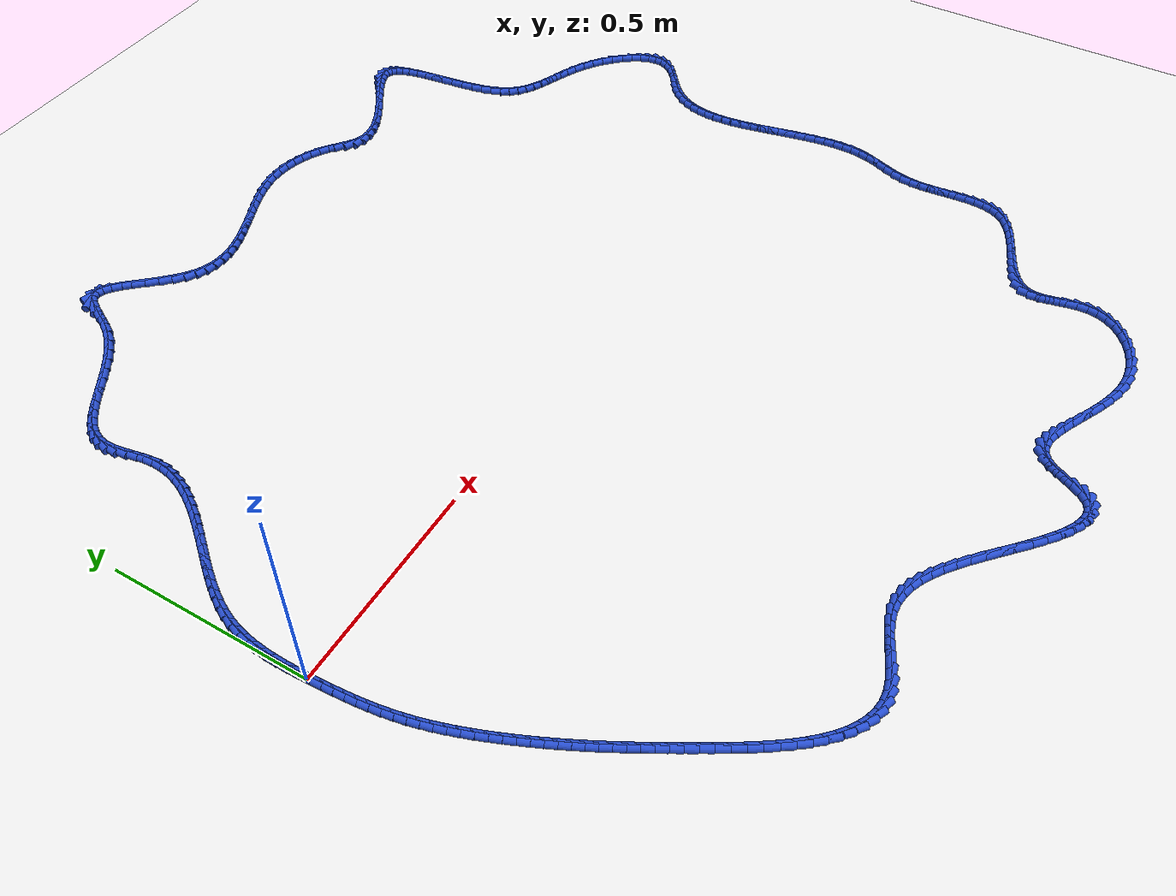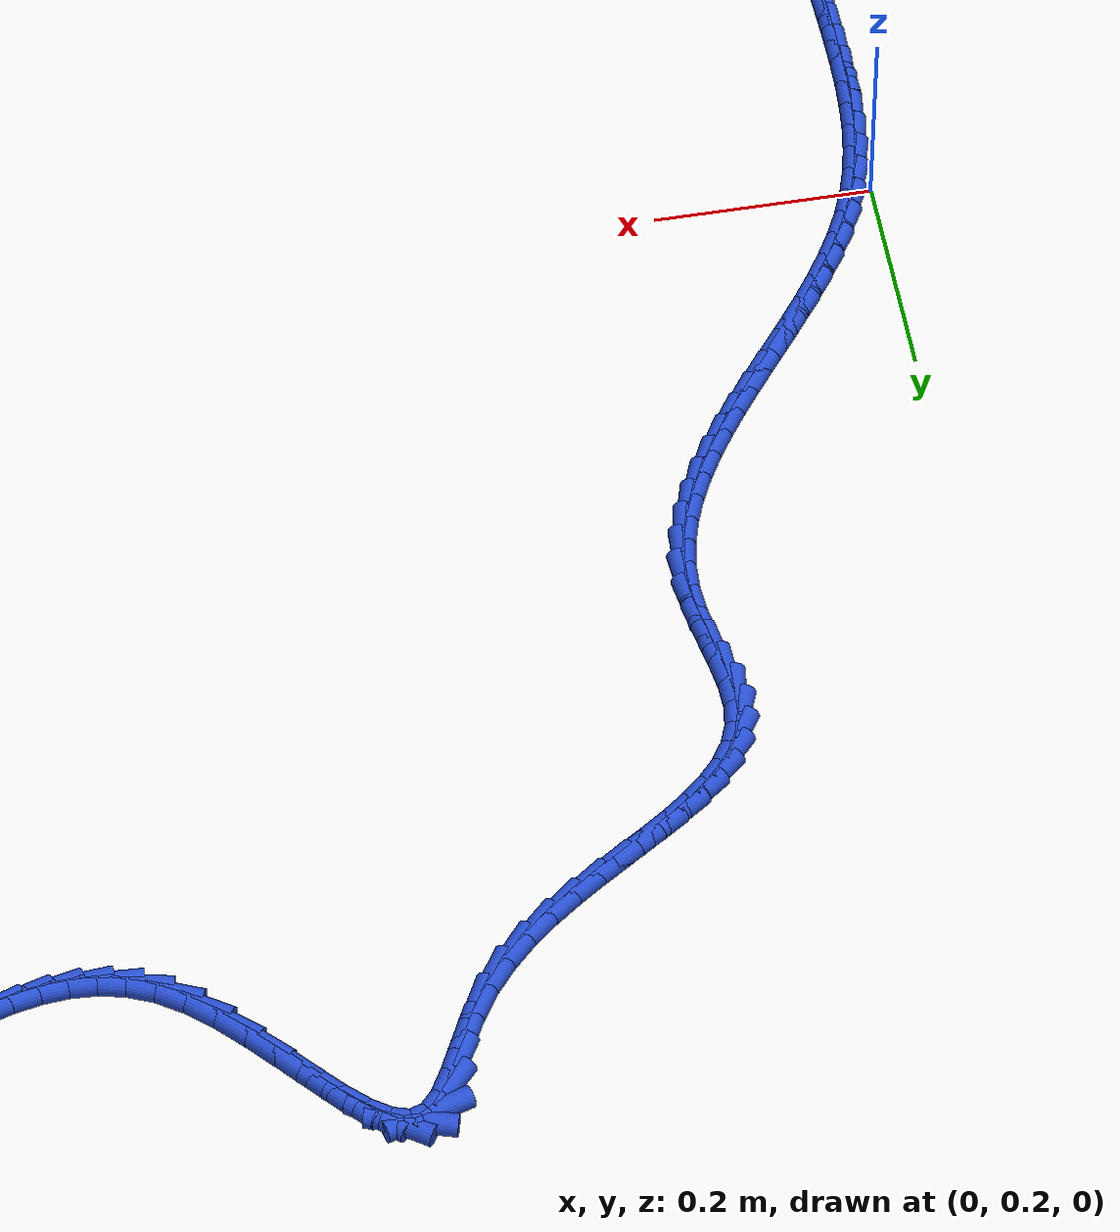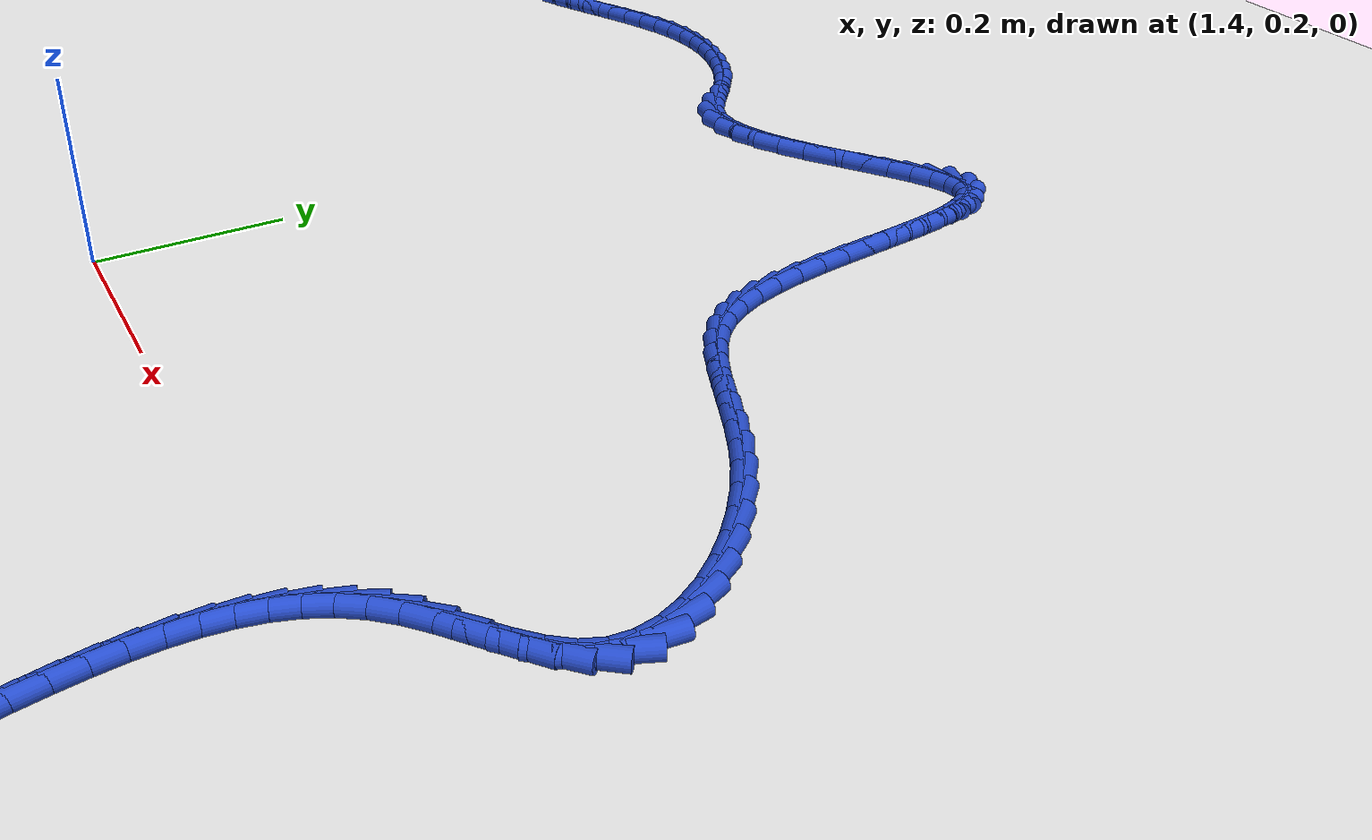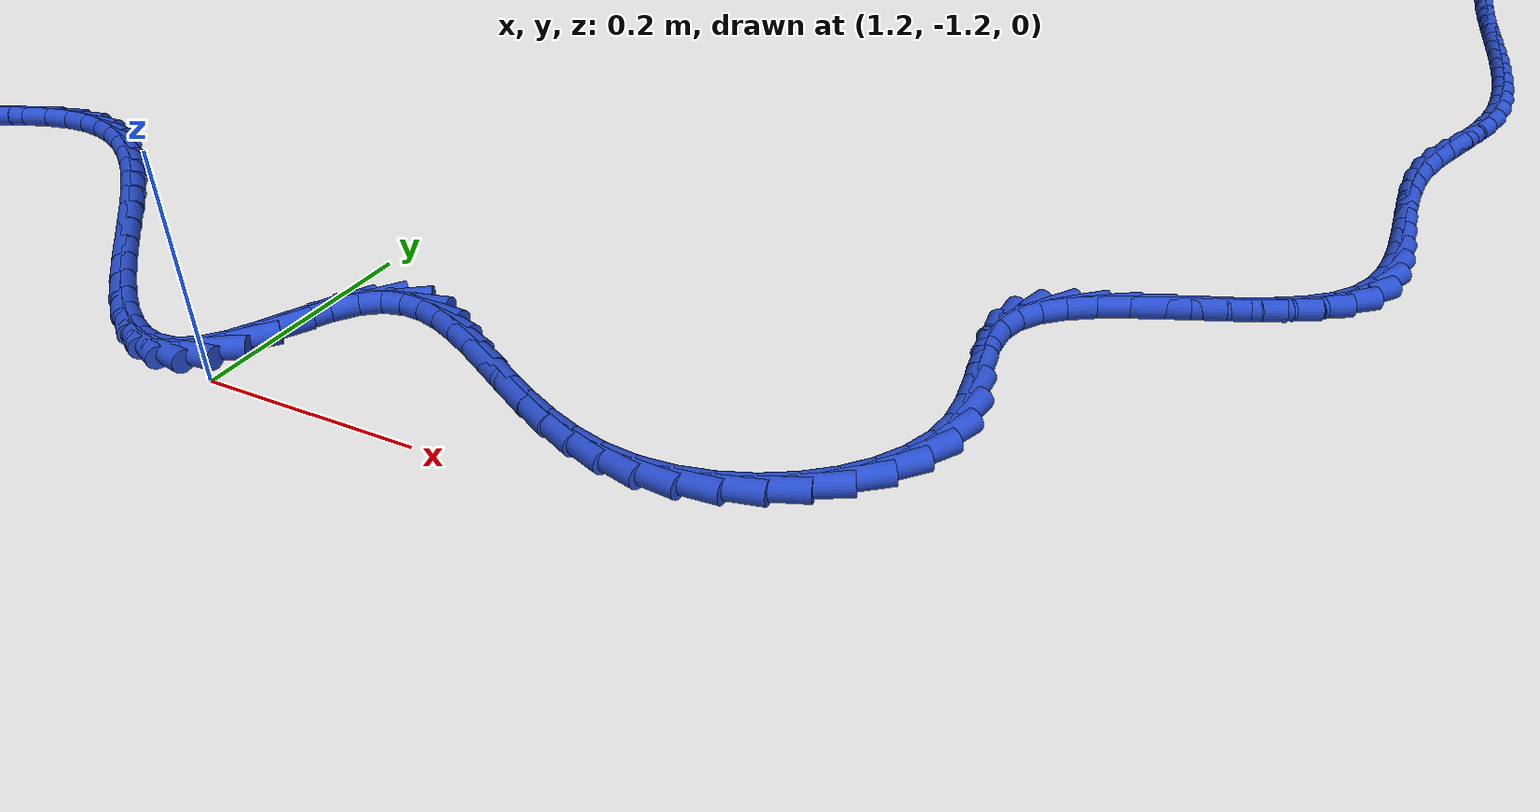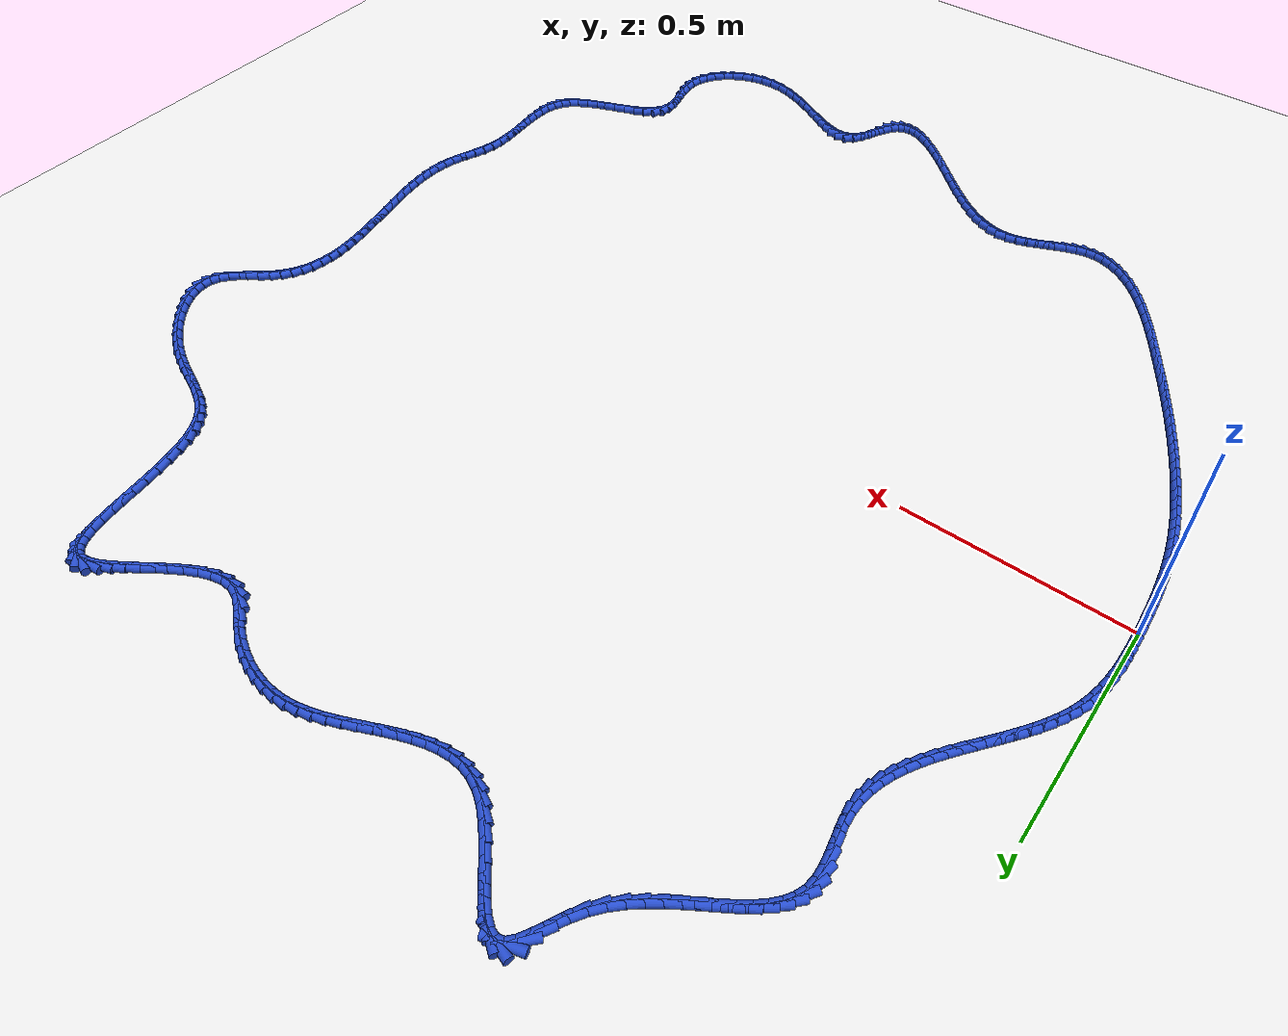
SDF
<sdf version="1.6">
 <world name="default">
  <light name="sun" type="directional">
   <pose>0 0 10 0 -0 0</pose>
   <diffuse>0.8 0.8 0.8 1</diffuse>
   <specular>0.2 0.2 0.2 1</specular>
   <attenuation>
    <range>1000</range>
    <constant>0.9</constant>
    <linear>0.01</linear>
    <quadratic>0.001</quadratic>
   </attenuation>
   <direction>-0.5 0.1 -0.9</direction>
  </light>
  <model name="ground_plane">
   <static>1</static>
   <link name="link">
    <collision name="collision">
     <geometry><plane><normal>0 0 1</normal><size>100 100</size></plane></geometry>
     <surface><friction><ode><mu>100</mu><mu2>50</mu2></ode></friction></surface>
    </collision>
    <visual name="visual">
     <cast_shadows>0</cast_shadows>
     <geometry><plane><normal>0 0 1</normal><size>100 100</size></plane></geometry>
     <material>
      <script><uri>file://media/materials/scripts/gazebo.material</uri><name>Gazebo/WhiteGlow</name></script>
     </material>
    </visual>
   </link>
  </model>
  <gravity>0 0 -9.8</gravity>
  <magnetic_field>6e-06 2.3e-05 -4.2e-05</magnetic_field>
  <atmosphere type="adiabatic"/>
  <physics name="default_physics" default="0" type="ode">
   <max_step_size>0.001</max_step_size>
   <real_time_factor>1</real_time_factor>
   <real_time_update_rate>1000</real_time_update_rate>
  </physics>
  <scene><ambient>0.4 0.4 0.4 1</ambient><background>0.7 0.7 0.7 1</background><shadows>1</shadows></scene>
  <spherical_coordinates>
   <surface_model>EARTH_WGS84</surface_model>
   <latitude_deg>0</latitude_deg>
   <longitude_deg>0</longitude_deg>
   <elevation>0</elevation>
   <heading_deg>0</heading_deg>
  </spherical_coordinates>
  <model name="line">
   <link name="link_0">
    <pose>3.686287386450715e-18 -6.938893903907228e-18 0.01 0 1.57 -1.5429442170032874</pose>
    <collision name="collision">
     <geometry><cylinder><radius>0.01</radius><length>0.08</length></cylinder></geometry>
    </collision>
    <visual name="visual">
     <material>
      <script><name>Gazebo/Blue</name><uri>file://media/materials/scripts/gazebo.material</uri></script>
     </material>
     <geometry><cylinder><radius>0.01</radius><length>0.08</length></cylinder></geometry>
    </visual>
   </link>
   <link name="link_1">
    <pose>-0.0007413888448551236 0.026611884419287215 0.01 0 1.57 -1.5613368921261304</pose>
    <collision name="collision">
     <geometry><cylinder><radius>0.01</radius><length>0.08</length></cylinder></geometry>
    </collision>
    <visual name="visual">
     <material>
      <script><name>Gazebo/Blue</name><uri>file://media/materials/scripts/gazebo.material</uri></script>
     </material>
     <geometry><cylinder><radius>0.01</radius><length>0.08</length></cylinder></geometry>
    </visual>
   </link>
   <link name="link_2">
    <pose>-0.000993579345261635 0.05327129770497839 0.01 0 1.57 1.5529341268489962</pose>
    <collision name="collision">
     <geometry><cylinder><radius>0.01</radius><length>0.08</length></cylinder></geometry>
    </collision>
    <visual name="visual">
     <material>
      <script><name>Gazebo/Blue</name><uri>file://media/materials/scripts/gazebo.material</uri></script>
     </material>
     <geometry><cylinder><radius>0.01</radius><length>0.08</length></cylinder></geometry>
    </visual>
   </link>
   <link name="link_3">
    <pose>-0.0005182153270759258 0.07988131563610236 0.01 0 1.57 1.5163877474611058</pose>
    <collision name="collision">
     <geometry><cylinder><radius>0.01</radius><length>0.08</length></cylinder></geometry>
    </collision>
    <visual name="visual">
     <material>
      <script><name>Gazebo/Blue</name><uri>file://media/materials/scripts/gazebo.material</uri></script>
     </material>
     <geometry><cylinder><radius>0.01</radius><length>0.08</length></cylinder></geometry>
    </visual>
   </link>
   <link name="link_4">
    <pose>0.0009230593838456076 0.10634501399168801 0.01 0 1.57 1.470240526559874</pose>
    <collision name="collision">
     <geometry><cylinder><radius>0.01</radius><length>0.08</length></cylinder></geometry>
    </collision>
    <visual name="visual">
     <material>
      <script><name>Gazebo/Blue</name><uri>file://media/materials/scripts/gazebo.material</uri></script>
     </material>
     <geometry><cylinder><radius>0.01</radius><length>0.08</length></cylinder></geometry>
    </visual>
   </link>
   <link name="link_5">
    <pose>0.003568600961646568 0.13256546855076415 0.01 0 1.57 1.4141264561284386</pose>
    <collision name="collision">
     <geometry><cylinder><radius>0.01</radius><length>0.08</length></cylinder></geometry>
    </collision>
    <visual name="visual">
     <material>
      <script><name>Gazebo/Blue</name><uri>file://media/materials/scripts/gazebo.material</uri></script>
     </material>
     <geometry><cylinder><radius>0.01</radius><length>0.08</length></cylinder></geometry>
    </visual>
   </link>
   <link name="link_6">
    <pose>0.007656765580470563 0.15844575509235964 0.01 0 1.57 1.347820590672643</pose>
    <collision name="collision">
     <geometry><cylinder><radius>0.01</radius><length>0.08</length></cylinder></geometry>
    </collision>
    <visual name="visual">
     <material>
      <script><name>Gazebo/Blue</name><uri>file://media/materials/scripts/gazebo.material</uri></script>
     </material>
     <geometry><cylinder><radius>0.01</radius><length>0.08</length></cylinder></geometry>
    </visual>
   </link>
   <link name="link_7">
    <pose>0.013425909414461193 0.18388894939550335 0.01 0 1.57 1.2714131816787544</pose>
    <collision name="collision">
     <geometry><cylinder><radius>0.01</radius><length>0.08</length></cylinder></geometry>
    </collision>
    <visual name="visual">
     <material>
      <script><name>Gazebo/Blue</name><uri>file://media/materials/scripts/gazebo.material</uri></script>
     </material>
     <geometry><cylinder><radius>0.01</radius><length>0.08</length></cylinder></geometry>
    </visual>
   </link>
   <link name="link_8">
    <pose>0.02111438863776207 0.20879812723922409 0.01 0 1.57 1.1870497626984773</pose>
    <collision name="collision">
     <geometry><cylinder><radius>0.01</radius><length>0.08</length></cylinder></geometry>
    </collision>
    <visual name="visual">
     <material>
      <script><name>Gazebo/Blue</name><uri>file://media/materials/scripts/gazebo.material</uri></script>
     </material>
     <geometry><cylinder><radius>0.01</radius><length>0.08</length></cylinder></geometry>
    </visual>
   </link>
   <link name="link_9">
    <pose>0.030922170363403986 0.2330890340069633 0.01 0 1.57 1.1091262469277718</pose>
    <collision name="collision">
     <geometry><cylinder><radius>0.01</radius><length>0.08</length></cylinder></geometry>
    </collision>
    <visual name="visual">
     <material>
      <script><name>Gazebo/Blue</name><uri>file://media/materials/scripts/gazebo.material</uri></script>
     </material>
     <geometry><cylinder><radius>0.01</radius><length>0.08</length></cylinder></geometry>
    </visual>
   </link>
   <link name="link_10">
    <pose>0.04271327307097997 0.25678828875724674 0.01 0 1.57 1.044774451590658</pose>
    <collision name="collision">
     <geometry><cylinder><radius>0.01</radius><length>0.08</length></cylinder></geometry>
    </collision>
    <visual name="visual">
     <material>
      <script><name>Gazebo/Blue</name><uri>file://media/materials/scripts/gazebo.material</uri></script>
     </material>
     <geometry><cylinder><radius>0.01</radius><length>0.08</length></cylinder></geometry>
    </visual>
   </link>
   <link name="link_11">
    <pose>0.05617796223108827 0.2799798545373734 0.01 0 1.57 0.9935671619011062</pose>
    <collision name="collision">
     <geometry><cylinder><radius>0.01</radius><length>0.08</length></cylinder></geometry>
    </collision>
    <visual name="visual">
     <material>
      <script><name>Gazebo/Blue</name><uri>file://media/materials/scripts/gazebo.material</uri></script>
     </material>
     <geometry><cylinder><radius>0.01</radius><length>0.08</length></cylinder></geometry>
    </visual>
   </link>
   <link name="link_12">
    <pose>0.07100504404337767 0.30274817600021203 0.01 0 1.57 0.9547754643559948</pose>
    <collision name="collision">
     <geometry><cylinder><radius>0.01</radius><length>0.08</length></cylinder></geometry>
    </collision>
    <visual name="visual">
     <material>
      <script><name>Gazebo/Blue</name><uri>file://media/materials/scripts/gazebo.material</uri></script>
     </material>
     <geometry><cylinder><radius>0.01</radius><length>0.08</length></cylinder></geometry>
    </visual>
   </link>
   <link name="link_13">
    <pose>0.086883324707497 0.32517769779863154 0.01 0 1.57 0.9276730989702013</pose>
    <collision name="collision">
     <geometry><cylinder><radius>0.01</radius><length>0.08</length></cylinder></geometry>
    </collision>
    <visual name="visual">
     <material>
      <script><name>Gazebo/Blue</name><uri>file://media/materials/scripts/gazebo.material</uri></script>
     </material>
     <geometry><cylinder><radius>0.01</radius><length>0.08</length></cylinder></geometry>
    </visual>
   </link>
   <link name="link_14">
    <pose>0.10350161042309504 0.34735286458550085 0.01 0 1.57 0.9116843677062412</pose>
    <collision name="collision">
     <geometry><cylinder><radius>0.01</radius><length>0.08</length></cylinder></geometry>
    </collision>
    <visual name="visual">
     <material>
      <script><name>Gazebo/Blue</name><uri>file://media/materials/scripts/gazebo.material</uri></script>
     </material>
     <geometry><cylinder><radius>0.01</radius><length>0.08</length></cylinder></geometry>
    </visual>
   </link>
   <link name="link_15">
    <pose>0.12054870738982067 0.36935812101368887 0.01 0 1.57 0.9064645990081811</pose>
    <collision name="collision">
     <geometry><cylinder><radius>0.01</radius><length>0.08</length></cylinder></geometry>
    </collision>
    <visual name="visual">
     <material>
      <script><name>Gazebo/Blue</name><uri>file://media/materials/scripts/gazebo.material</uri></script>
     </material>
     <geometry><cylinder><radius>0.01</radius><length>0.08</length></cylinder></geometry>
    </visual>
   </link>
   <link name="link_16">
    <pose>0.13771342180732257 0.39127791173606435 0.01 0 1.57 0.9119398595168361</pose>
    <collision name="collision">
     <geometry><cylinder><radius>0.01</radius><length>0.08</length></cylinder></geometry>
    </collision>
    <visual name="visual">
     <material>
      <script><name>Gazebo/Blue</name><uri>file://media/materials/scripts/gazebo.material</uri></script>
     </material>
     <geometry><cylinder><radius>0.01</radius><length>0.08</length></cylinder></geometry>
    </visual>
   </link>
   <link name="link_17">
    <pose>0.15468455987524968 0.4131966814054964 0.01 0 1.57 0.9283221466589692</pose>
    <collision name="collision">
     <geometry><cylinder><radius>0.01</radius><length>0.08</length></cylinder></geometry>
    </collision>
    <visual name="visual">
     <material>
      <script><name>Gazebo/Blue</name><uri>file://media/materials/scripts/gazebo.material</uri></script>
     </material>
     <geometry><cylinder><radius>0.01</radius><length>0.08</length></cylinder></geometry>
    </visual>
   </link>
   <link name="link_18">
    <pose>0.17115092779325067 0.4351988746748538 0.01 0 1.57 0.9561048122682099</pose>
    <collision name="collision">
     <geometry><cylinder><radius>0.01</radius><length>0.08</length></cylinder></geometry>
    </collision>
    <visual name="visual">
     <material>
      <script><name>Gazebo/Blue</name><uri>file://media/materials/scripts/gazebo.material</uri></script>
     </material>
     <geometry><cylinder><radius>0.01</radius><length>0.08</length></cylinder></geometry>
    </visual>
   </link>
   <link name="link_19">
    <pose>0.1868013317609745 0.45736893619700547 0.01 0 1.57 0.9960310596495743</pose>
    <collision name="collision">
     <geometry><cylinder><radius>0.01</radius><length>0.08</length></cylinder></geometry>
    </collision>
    <visual name="visual">
     <material>
      <script><name>Gazebo/Blue</name><uri>file://media/materials/scripts/gazebo.material</uri></script>
     </material>
     <geometry><cylinder><radius>0.01</radius><length>0.08</length></cylinder></geometry>
    </visual>
   </link>
   <link name="link_20">
    <pose>0.2013245779780699 0.4797913106248205 0.01 0 1.57 1.0490150875931776</pose>
    <collision name="collision">
     <geometry><cylinder><radius>0.01</radius><length>0.08</length></cylinder></geometry>
    </collision>
    <visual name="visual">
     <material>
      <script><name>Gazebo/Blue</name><uri>file://media/materials/scripts/gazebo.material</uri></script>
     </material>
     <geometry><cylinder><radius>0.01</radius><length>0.08</length></cylinder></geometry>
    </visual>
   </link>
   <link name="link_21">
    <pose>0.21440947264418564 0.5025504426111673 0.01 0 1.57 1.1159816032242178</pose>
    <collision name="collision">
     <geometry><cylinder><radius>0.01</radius><length>0.08</length></cylinder></geometry>
    </collision>
    <visual name="visual">
     <material>
      <script><name>Gazebo/Blue</name><uri>file://media/materials/scripts/gazebo.material</uri></script>
     </material>
     <geometry><cylinder><radius>0.01</radius><length>0.08</length></cylinder></geometry>
    </visual>
   </link>
   <link name="link_22">
    <pose>0.22574482195897055 0.525730776808915 0.01 0 1.57 1.1975822549678123</pose>
    <collision name="collision">
     <geometry><cylinder><radius>0.01</radius><length>0.08</length></cylinder></geometry>
    </collision>
    <visual name="visual">
     <material>
      <script><name>Gazebo/Blue</name><uri>file://media/materials/scripts/gazebo.material</uri></script>
     </material>
     <geometry><cylinder><radius>0.01</radius><length>0.08</length></cylinder></geometry>
    </visual>
   </link>
   <link name="link_23">
    <pose>0.23501943212207346 0.5494167578709327 0.01 0 1.57 1.29376698057198</pose>
    <collision name="collision">
     <geometry><cylinder><radius>0.01</radius><length>0.08</length></cylinder></geometry>
    </collision>
    <visual name="visual">
     <material>
      <script><name>Gazebo/Blue</name><uri>file://media/materials/scripts/gazebo.material</uri></script>
     </material>
     <geometry><cylinder><radius>0.01</radius><length>0.08</length></cylinder></geometry>
    </visual>
   </link>
   <link name="link_24">
    <pose>0.24192210933314323 0.5736928304500892 0.01 0 1.57 1.403265335978539</pose>
    <collision name="collision">
     <geometry><cylinder><radius>0.01</radius><length>0.08</length></cylinder></geometry>
    </collision>
    <visual name="visual">
     <material>
      <script><name>Gazebo/Blue</name><uri>file://media/materials/scripts/gazebo.material</uri></script>
     </material>
     <geometry><cylinder><radius>0.01</radius><length>0.08</length></cylinder></geometry>
    </visual>
   </link>
   <link name="link_25">
    <pose>0.2461416597918286 0.5986434391992534 0.01 0 1.57 1.5231758229309047</pose>
    <collision name="collision">
     <geometry><cylinder><radius>0.01</radius><length>0.08</length></cylinder></geometry>
    </collision>
    <visual name="visual">
     <material>
      <script><name>Gazebo/Blue</name><uri>file://media/materials/scripts/gazebo.material</uri></script>
     </material>
     <geometry><cylinder><radius>0.01</radius><length>0.08</length></cylinder></geometry>
    </visual>
   </link>
   <link name="link_26">
    <pose>0.2473668896977783 0.624353028771294 0.01 0 1.57 -1.494933936933465</pose>
    <collision name="collision">
     <geometry><cylinder><radius>0.01</radius><length>0.08</length></cylinder></geometry>
    </collision>
    <visual name="visual">
     <material>
      <script><name>Gazebo/Blue</name><uri>file://media/materials/scripts/gazebo.material</uri></script>
     </material>
     <geometry><cylinder><radius>0.01</radius><length>0.08</length></cylinder></geometry>
    </visual>
   </link>
   <link name="link_27">
    <pose>0.24535043959928426 0.6508823844252022 0.01 0 1.57 -1.4087715480247576</pose>
    <collision name="collision">
     <geometry><cylinder><radius>0.01</radius><length>0.08</length></cylinder></geometry>
    </collision>
    <visual name="visual">
     <material>
      <script><name>Gazebo/Blue</name><uri>file://media/materials/scripts/gazebo.material</uri></script>
     </material>
     <geometry><cylinder><radius>0.01</radius><length>0.08</length></cylinder></geometry>
    </visual>
   </link>
   <link name="link_28">
    <pose>0.24093619177847547 0.6778878364745462 0.01 0 1.57 -1.384444427604644</pose>
    <collision name="collision">
     <geometry><cylinder><radius>0.01</radius><length>0.08</length></cylinder></geometry>
    </collision>
    <visual name="visual">
     <material>
      <script><name>Gazebo/Blue</name><uri>file://media/materials/scripts/gazebo.material</uri></script>
     </material>
     <geometry><cylinder><radius>0.01</radius><length>0.08</length></cylinder></geometry>
    </visual>
   </link>
   <link name="link_29">
    <pose>0.23588361206379785 0.7046863657727563 0.01 0 1.57 -1.4212126874905262</pose>
    <collision name="collision">
     <geometry><cylinder><radius>0.01</radius><length>0.08</length></cylinder></geometry>
    </collision>
    <visual name="visual">
     <material>
      <script><name>Gazebo/Blue</name><uri>file://media/materials/scripts/gazebo.material</uri></script>
     </material>
     <geometry><cylinder><radius>0.01</radius><length>0.08</length></cylinder></geometry>
    </visual>
   </link>
   <link name="link_30">
    <pose>0.23198052940571381 0.7305844407408563 0.01 0 1.57 -1.5310808358699863</pose>
    <collision name="collision">
     <geometry><cylinder><radius>0.01</radius><length>0.08</length></cylinder></geometry>
    </collision>
    <visual name="visual">
     <material>
      <script><name>Gazebo/Blue</name><uri>file://media/materials/scripts/gazebo.material</uri></script>
     </material>
     <geometry><cylinder><radius>0.01</radius><length>0.08</length></cylinder></geometry>
    </visual>
   </link>
   <link name="link_31">
    <pose>0.23101477275468582 0.7548885297998691 0.01 0 1.57 1.4130602434443644</pose>
    <collision name="collision">
     <geometry><cylinder><radius>0.01</radius><length>0.08</length></cylinder></geometry>
    </collision>
    <visual name="visual">
     <material>
      <script><name>Gazebo/Blue</name><uri>file://media/materials/scripts/gazebo.material</uri></script>
     </material>
     <geometry><cylinder><radius>0.01</radius><length>0.08</length></cylinder></geometry>
    </visual>
   </link>
   <link name="link_32">
    <pose>0.23453396850470723 0.7770138450539543 0.01 0 1.57 1.1893072501443114</pose>
    <collision name="collision">
     <geometry><cylinder><radius>0.01</radius><length>0.08</length></cylinder></geometry>
    </collision>
    <visual name="visual">
     <material>
      <script><name>Gazebo/Blue</name><uri>file://media/materials/scripts/gazebo.material</uri></script>
     </material>
     <geometry><cylinder><radius>0.01</radius><length>0.08</length></cylinder></geometry>
    </visual>
   </link>
   <link name="link_33">
    <pose>0.242575088873368 0.7970594968201021 0.01 0 1.57 0.9906154916773493</pose>
    <collision name="collision">
     <geometry><cylinder><radius>0.01</radius><length>0.08</length></cylinder></geometry>
    </collision>
    <visual name="visual">
     <material>
      <script><name>Gazebo/Blue</name><uri>file://media/materials/scripts/gazebo.material</uri></script>
     </material>
     <geometry><cylinder><radius>0.01</radius><length>0.08</length></cylinder></geometry>
    </visual>
   </link>
   <link name="link_34">
    <pose>0.25458927150356236 0.8153898124483653 0.01 0 1.57 0.8329544414922904</pose>
    <collision name="collision">
     <geometry><cylinder><radius>0.01</radius><length>0.08</length></cylinder></geometry>
    </collision>
    <visual name="visual">
     <material>
      <script><name>Gazebo/Blue</name><uri>file://media/materials/scripts/gazebo.material</uri></script>
     </material>
     <geometry><cylinder><radius>0.01</radius><length>0.08</length></cylinder></geometry>
    </visual>
   </link>
   <link name="link_35">
    <pose>0.27002636674127845 0.8323697020694663 0.01 0 1.57 0.7180018857014266</pose>
    <collision name="collision">
     <geometry><cylinder><radius>0.01</radius><length>0.08</length></cylinder></geometry>
    </collision>
    <visual name="visual">
     <material>
      <script><name>Gazebo/Blue</name><uri>file://media/materials/scripts/gazebo.material</uri></script>
     </material>
     <geometry><cylinder><radius>0.01</radius><length>0.08</length></cylinder></geometry>
    </visual>
   </link>
   <link name="link_36">
    <pose>0.2883362249325047 0.848364075814129 0.01 0 1.57 0.640373728744902</pose>
    <collision name="collision">
     <geometry><cylinder><radius>0.01</radius><length>0.08</length></cylinder></geometry>
    </collision>
    <visual name="visual">
     <material>
      <script><name>Gazebo/Blue</name><uri>file://media/materials/scripts/gazebo.material</uri></script>
     </material>
     <geometry><cylinder><radius>0.01</radius><length>0.08</length></cylinder></geometry>
    </visual>
   </link>
   <link name="link_37">
    <pose>0.30896869642322916 0.8637378438130758 0.01 0 1.57 0.5935884004744302</pose>
    <collision name="collision">
     <geometry><cylinder><radius>0.01</radius><length>0.08</length></cylinder></geometry>
    </collision>
    <visual name="visual">
     <material>
      <script><name>Gazebo/Blue</name><uri>file://media/materials/scripts/gazebo.material</uri></script>
     </material>
     <geometry><cylinder><radius>0.01</radius><length>0.08</length></cylinder></geometry>
    </visual>
   </link>
   <link name="link_38">
    <pose>0.33137363155943994 0.8788559161970296 0.01 0 1.57 0.5724848572416695</pose>
    <collision name="collision">
     <geometry><cylinder><radius>0.01</radius><length>0.08</length></cylinder></geometry>
    </collision>
    <visual name="visual">
     <material>
      <script><name>Gazebo/Blue</name><uri>file://media/materials/scripts/gazebo.material</uri></script>
     </material>
     <geometry><cylinder><radius>0.01</radius><length>0.08</length></cylinder></geometry>
    </visual>
   </link>
   <link name="link_39">
    <pose>0.3550008806871256 0.8940832030967137 0.01 0 1.57 0.573673986408293</pose>
    <collision name="collision">
     <geometry><cylinder><radius>0.01</radius><length>0.08</length></cylinder></geometry>
    </collision>
    <visual name="visual">
     <material>
      <script><name>Gazebo/Blue</name><uri>file://media/materials/scripts/gazebo.material</uri></script>
     </material>
     <geometry><cylinder><radius>0.01</radius><length>0.08</length></cylinder></geometry>
    </visual>
   </link>
   <link name="link_40">
    <pose>0.379300294152274 0.909784614642851 0.01 0 1.57 0.5953228110911825</pose>
    <collision name="collision">
     <geometry><cylinder><radius>0.01</radius><length>0.08</length></cylinder></geometry>
    </collision>
    <visual name="visual">
     <material>
      <script><name>Gazebo/Blue</name><uri>file://media/materials/scripts/gazebo.material</uri></script>
     </material>
     <geometry><cylinder><radius>0.01</radius><length>0.08</length></cylinder></geometry>
    </visual>
   </link>
   <link name="link_41">
    <pose>0.40372172230087355 0.9263250609661642 0.01 0 1.57 0.6367835692463997</pose>
    <collision name="collision">
     <geometry><cylinder><radius>0.01</radius><length>0.08</length></cylinder></geometry>
    </collision>
    <visual name="visual">
     <material>
      <script><name>Gazebo/Blue</name><uri>file://media/materials/scripts/gazebo.material</uri></script>
     </material>
     <geometry><cylinder><radius>0.01</radius><length>0.08</length></cylinder></geometry>
    </visual>
   </link>
   <link name="link_42">
    <pose>0.42771501547891244 0.9440694521973765 0.01 0 1.57 0.6981664038873943</pose>
    <collision name="collision">
     <geometry><cylinder><radius>0.01</radius><length>0.08</length></cylinder></geometry>
    </collision>
    <visual name="visual">
     <material>
      <script><name>Gazebo/Blue</name><uri>file://media/materials/scripts/gazebo.material</uri></script>
     </material>
     <geometry><cylinder><radius>0.01</radius><length>0.08</length></cylinder></geometry>
    </visual>
   </link>
   <link name="link_43">
    <pose>0.45073002403237855 0.9633826984672105 0.01 0 1.57 0.779792260635435</pose>
    <collision name="collision">
     <geometry><cylinder><radius>0.01</radius><length>0.08</length></cylinder></geometry>
    </collision>
    <visual name="visual">
     <material>
      <script><name>Gazebo/Blue</name><uri>file://media/materials/scripts/gazebo.material</uri></script>
     </material>
     <geometry><cylinder><radius>0.01</radius><length>0.08</length></cylinder></geometry>
    </visual>
   </link>
   <link name="link_44">
    <pose>0.4722165983072607 0.98462970990639 0.01 0 1.57 0.8814311253326867</pose>
    <collision name="collision">
     <geometry><cylinder><radius>0.01</radius><length>0.08</length></cylinder></geometry>
    </collision>
    <visual name="visual">
     <material>
      <script><name>Gazebo/Blue</name><uri>file://media/materials/scripts/gazebo.material</uri></script>
     </material>
     <geometry><cylinder><radius>0.01</radius><length>0.08</length></cylinder></geometry>
    </visual>
   </link>
   <link name="link_45">
    <pose>0.4916245886495465 1.0081753966456368 0.01 0 1.57 0.9994162548701124</pose>
    <collision name="collision">
     <geometry><cylinder><radius>0.01</radius><length>0.08</length></cylinder></geometry>
    </collision>
    <visual name="visual">
     <material>
      <script><name>Gazebo/Blue</name><uri>file://media/materials/scripts/gazebo.material</uri></script>
     </material>
     <geometry><cylinder><radius>0.01</radius><length>0.08</length></cylinder></geometry>
    </visual>
   </link>
   <link name="link_46">
    <pose>0.508434108664295 1.0343210906718612 0.01 0 1.57 1.087511052399249</pose>
    <collision name="collision">
     <geometry><cylinder><radius>0.01</radius><length>0.08</length></cylinder></geometry>
    </collision>
    <visual name="visual">
     <material>
      <script><name>Gazebo/Blue</name><uri>file://media/materials/scripts/gazebo.material</uri></script>
     </material>
     <geometry><cylinder><radius>0.01</radius><length>0.08</length></cylinder></geometry>
    </visual>
   </link>
   <link name="link_47">
    <pose>0.5228636943702706 1.061816819589835 0.01 0 1.57 1.1060948280510068</pose>
    <collision name="collision">
     <geometry><cylinder><radius>0.01</radius><length>0.08</length></cylinder></geometry>
    </collision>
    <visual name="visual">
     <material>
      <script><name>Gazebo/Blue</name><uri>file://media/materials/scripts/gazebo.material</uri></script>
     </material>
     <geometry><cylinder><radius>0.01</radius><length>0.08</length></cylinder></geometry>
    </visual>
   </link>
   <link name="link_48">
    <pose>0.5358946379844565 1.0878101853319329 0.01 0 1.57 1.040328941499191</pose>
    <collision name="collision">
     <geometry><cylinder><radius>0.01</radius><length>0.08</length></cylinder></geometry>
    </collision>
    <visual name="visual">
     <material>
      <script><name>Gazebo/Blue</name><uri>file://media/materials/scripts/gazebo.material</uri></script>
     </material>
     <geometry><cylinder><radius>0.01</radius><length>0.08</length></cylinder></geometry>
    </visual>
   </link>
   <link name="link_49">
    <pose>0.5485433633436336 1.1093749840592864 0.01 0 1.57 0.8191066402095308</pose>
    <collision name="collision">
     <geometry><cylinder><radius>0.01</radius><length>0.08</length></cylinder></geometry>
    </collision>
    <visual name="visual">
     <material>
      <script><name>Gazebo/Blue</name><uri>file://media/materials/scripts/gazebo.material</uri></script>
     </material>
     <geometry><cylinder><radius>0.01</radius><length>0.08</length></cylinder></geometry>
    </visual>
   </link>
   <link name="link_50">
    <pose>0.5618262942845831 1.1235850119330275 0.01 0 1.57 0.28967364256238726</pose>
    <collision name="collision">
     <geometry><cylinder><radius>0.01</radius><length>0.08</length></cylinder></geometry>
    </collision>
    <visual name="visual">
     <material>
      <script><name>Gazebo/Blue</name><uri>file://media/materials/scripts/gazebo.material</uri></script>
     </material>
     <geometry><cylinder><radius>0.01</radius><length>0.08</length></cylinder></geometry>
    </visual>
   </link>
   <link name="link_51">
    <pose>0.5766376961548272 1.1279996598876025 0.01 0 1.57 -0.28343651736742365</pose>
    <collision name="collision">
     <geometry><cylinder><radius>0.01</radius><length>0.08</length></cylinder></geometry>
    </collision>
    <visual name="visual">
     <material>
      <script><name>Gazebo/Blue</name><uri>file://media/materials/scripts/gazebo.material</uri></script>
     </material>
     <geometry><cylinder><radius>0.01</radius><length>0.08</length></cylinder></geometry>
    </visual>
   </link>
   <link name="link_52">
    <pose>0.5931113772725999 1.123201227547556 0.01 0 1.57 -0.5988150294666741</pose>
    <collision name="collision">
     <geometry><cylinder><radius>0.01</radius><length>0.08</length></cylinder></geometry>
    </collision>
    <visual name="visual">
     <material>
      <script><name>Gazebo/Blue</name><uri>file://media/materials/scripts/gazebo.material</uri></script>
     </material>
     <geometry><cylinder><radius>0.01</radius><length>0.08</length></cylinder></geometry>
    </visual>
   </link>
   <link name="link_53">
    <pose>0.6110890023099238 1.1109333208741223 0.01 0 1.57 -0.7497360749046943</pose>
    <collision name="collision">
     <geometry><cylinder><radius>0.01</radius><length>0.08</length></cylinder></geometry>
    </collision>
    <visual name="visual">
     <material>
      <script><name>Gazebo/Blue</name><uri>file://media/materials/scripts/gazebo.material</uri></script>
     </material>
     <geometry><cylinder><radius>0.01</radius><length>0.08</length></cylinder></geometry>
    </visual>
   </link>
   <link name="link_54">
    <pose>0.6304116306218182 1.0929419520368484 0.01 0 1.57 -0.8197587748956852</pose>
    <collision name="collision">
     <geometry><cylinder><radius>0.01</radius><length>0.08</length></cylinder></geometry>
    </collision>
    <visual name="visual">
     <material>
      <script><name>Gazebo/Blue</name><uri>file://media/materials/scripts/gazebo.material</uri></script>
     </material>
     <geometry><cylinder><radius>0.01</radius><length>0.08</length></cylinder></geometry>
    </visual>
   </link>
   <link name="link_55">
    <pose>0.6509203215633032 1.0709731332052836 0.01 0 1.57 -0.8435893376191165</pose>
    <collision name="collision">
     <geometry><cylinder><radius>0.01</radius><length>0.08</length></cylinder></geometry>
    </collision>
    <visual name="visual">
     <material>
      <script><name>Gazebo/Blue</name><uri>file://media/materials/scripts/gazebo.material</uri></script>
     </material>
     <geometry><cylinder><radius>0.01</radius><length>0.08</length></cylinder></geometry>
    </visual>
   </link>
   <link name="link_56">
    <pose>0.6724561344893986 1.0467728765489757 0.01 0 1.57 -0.8338143996841013</pose>
    <collision name="collision">
     <geometry><cylinder><radius>0.01</radius><length>0.08</length></cylinder></geometry>
    </collision>
    <visual name="visual">
     <material>
      <script><name>Gazebo/Blue</name><uri>file://media/materials/scripts/gazebo.material</uri></script>
     </material>
     <geometry><cylinder><radius>0.01</radius><length>0.08</length></cylinder></geometry>
    </visual>
   </link>
   <link name="link_57">
    <pose>0.6948601287551242 1.0220871942374734 0.01 0 1.57 -0.7920992238722865</pose>
    <collision name="collision">
     <geometry><cylinder><radius>0.01</radius><length>0.08</length></cylinder></geometry>
    </collision>
    <visual name="visual">
     <material>
      <script><name>Gazebo/Blue</name><uri>file://media/materials/scripts/gazebo.material</uri></script>
     </material>
     <geometry><cylinder><radius>0.01</radius><length>0.08</length></cylinder></geometry>
    </visual>
   </link>
   <link name="link_58">
    <pose>0.7179733637154994 0.998662098440325 0.01 0 1.57 -0.7119170840673851</pose>
    <collision name="collision">
     <geometry><cylinder><radius>0.01</radius><length>0.08</length></cylinder></geometry>
    </collision>
    <visual name="visual">
     <material>
      <script><name>Gazebo/Blue</name><uri>file://media/materials/scripts/gazebo.material</uri></script>
     </material>
     <geometry><cylinder><radius>0.01</radius><length>0.08</length></cylinder></geometry>
    </visual>
   </link>
   <link name="link_59">
    <pose>0.741636898725544 0.9782436013270788 0.01 0 1.57 -0.5785331346976742</pose>
    <collision name="collision">
     <geometry><cylinder><radius>0.01</radius><length>0.08</length></cylinder></geometry>
    </collision>
    <visual name="visual">
     <material>
      <script><name>Gazebo/Blue</name><uri>file://media/materials/scripts/gazebo.material</uri></script>
     </material>
     <geometry><cylinder><radius>0.01</radius><length>0.08</length></cylinder></geometry>
    </visual>
   </link>
   <link name="link_60">
    <pose>0.7656945539928224 0.9625321733921062 0.01 0 1.57 -0.40355195338283684</pose>
    <collision name="collision">
     <geometry><cylinder><radius>0.01</radius><length>0.08</length></cylinder></geometry>
    </collision>
    <visual name="visual">
     <material>
      <script><name>Gazebo/Blue</name><uri>file://media/materials/scripts/gazebo.material</uri></script>
     </material>
     <geometry><cylinder><radius>0.01</radius><length>0.08</length></cylinder></geometry>
    </visual>
   </link>
   <link name="link_61">
    <pose>0.7900567395955146 0.9521298511463018 0.01 0 1.57 -0.2241500601812755</pose>
    <collision name="collision">
     <geometry><cylinder><radius>0.01</radius><length>0.08</length></cylinder></geometry>
    </collision>
    <visual name="visual">
     <material>
      <script><name>Gazebo/Blue</name><uri>file://media/materials/scripts/gazebo.material</uri></script>
     </material>
     <geometry><cylinder><radius>0.01</radius><length>0.08</length></cylinder></geometry>
    </visual>
   </link>
   <link name="link_62">
    <pose>0.8147022189312214 0.946511148126872 0.01 0 1.57 -0.0566192326462113</pose>
    <collision name="collision">
     <geometry><cylinder><radius>0.01</radius><length>0.08</length></cylinder></geometry>
    </collision>
    <visual name="visual">
     <material>
      <script><name>Gazebo/Blue</name><uri>file://media/materials/scripts/gazebo.material</uri></script>
     </material>
     <geometry><cylinder><radius>0.01</radius><length>0.08</length></cylinder></geometry>
    </visual>
   </link>
   <link name="link_63">
    <pose>0.8396128690153837 0.9450992171518168 0.01 0 1.57 0.08793625953918975</pose>
    <collision name="collision">
     <geometry><cylinder><radius>0.01</radius><length>0.08</length></cylinder></geometry>
    </collision>
    <visual name="visual">
     <material>
      <script><name>Gazebo/Blue</name><uri>file://media/materials/scripts/gazebo.material</uri></script>
     </material>
     <geometry><cylinder><radius>0.01</radius><length>0.08</length></cylinder></geometry>
    </visual>
   </link>
   <link name="link_64">
    <pose>0.864770566863442 0.9473172110391358 0.01 0 1.57 0.2047229971440268</pose>
    <collision name="collision">
     <geometry><cylinder><radius>0.01</radius><length>0.08</length></cylinder></geometry>
    </collision>
    <visual name="visual">
     <material>
      <script><name>Gazebo/Blue</name><uri>file://media/materials/scripts/gazebo.material</uri></script>
     </material>
     <geometry><cylinder><radius>0.01</radius><length>0.08</length></cylinder></geometry>
    </visual>
   </link>
   <link name="link_65">
    <pose>0.8901571894908371 0.9525882826068293 0.01 0 1.57 0.29389485561547296</pose>
    <collision name="collision">
     <geometry><cylinder><radius>0.01</radius><length>0.08</length></cylinder></geometry>
    </collision>
    <visual name="visual">
     <material>
      <script><name>Gazebo/Blue</name><uri>file://media/materials/scripts/gazebo.material</uri></script>
     </material>
     <geometry><cylinder><radius>0.01</radius><length>0.08</length></cylinder></geometry>
    </visual>
   </link>
   <link name="link_66">
    <pose>0.9157546139130097 0.9603355846728961 0.01 0 1.57 0.35793403908037064</pose>
    <collision name="collision">
     <geometry><cylinder><radius>0.01</radius><length>0.08</length></cylinder></geometry>
    </collision>
    <visual name="visual">
     <material>
      <script><name>Gazebo/Blue</name><uri>file://media/materials/scripts/gazebo.material</uri></script>
     </material>
     <geometry><cylinder><radius>0.01</radius><length>0.08</length></cylinder></geometry>
    </visual>
   </link>
   <link name="link_67">
    <pose>0.9415447171454006 0.9699822700553372 0.01 0 1.57 0.39972354235509167</pose>
    <collision name="collision">
     <geometry><cylinder><radius>0.01</radius><length>0.08</length></cylinder></geometry>
    </collision>
    <visual name="visual">
     <material>
      <script><name>Gazebo/Blue</name><uri>file://media/materials/scripts/gazebo.material</uri></script>
     </material>
     <geometry><cylinder><radius>0.01</radius><length>0.08</length></cylinder></geometry>
    </visual>
   </link>
   <link name="link_68">
    <pose>0.9675093762034503 0.9809514915721517 0.01 0 1.57 0.4215931000063918</pose>
    <collision name="collision">
     <geometry><cylinder><radius>0.01</radius><length>0.08</length></cylinder></geometry>
    </collision>
    <visual name="visual">
     <material>
      <script><name>Gazebo/Blue</name><uri>file://media/materials/scripts/gazebo.material</uri></script>
     </material>
     <geometry><cylinder><radius>0.01</radius><length>0.08</length></cylinder></geometry>
    </visual>
   </link>
   <link name="link_69">
    <pose>0.9936304681025997 0.9926664020413394 0.01 0 1.57 0.4249743791228145</pose>
    <collision name="collision">
     <geometry><cylinder><radius>0.01</radius><length>0.08</length></cylinder></geometry>
    </collision>
    <visual name="visual">
     <material>
      <script><name>Gazebo/Blue</name><uri>file://media/materials/scripts/gazebo.material</uri></script>
     </material>
     <geometry><cylinder><radius>0.01</radius><length>0.08</length></cylinder></geometry>
    </visual>
   </link>
   <link name="link_70">
    <pose>1.0198898698582892 1.0045501542809 0.01 0 1.57 0.4103301031132899</pose>
    <collision name="collision">
     <geometry><cylinder><radius>0.01</radius><length>0.08</length></cylinder></geometry>
    </collision>
    <visual name="visual">
     <material>
      <script><name>Gazebo/Blue</name><uri>file://media/materials/scripts/gazebo.material</uri></script>
     </material>
     <geometry><cylinder><radius>0.01</radius><length>0.08</length></cylinder></geometry>
    </visual>
   </link>
   <link name="link_71">
    <pose>1.0462694584859602 1.016025901108834 0.01 0 1.57 0.37718913463953535</pose>
    <collision name="collision">
     <geometry><cylinder><radius>0.01</radius><length>0.08</length></cylinder></geometry>
    </collision>
    <visual name="visual">
     <material>
      <script><name>Gazebo/Blue</name><uri>file://media/materials/scripts/gazebo.material</uri></script>
     </material>
     <geometry><cylinder><radius>0.01</radius><length>0.08</length></cylinder></geometry>
    </visual>
   </link>
   <link name="link_72">
    <pose>1.0727511110010526 1.0265167953431402 0.01 0 1.57 0.3242553448324908</pose>
    <collision name="collision">
     <geometry><cylinder><radius>0.01</radius><length>0.08</length></cylinder></geometry>
    </collision>
    <visual name="visual">
     <material>
      <script><name>Gazebo/Blue</name><uri>file://media/materials/scripts/gazebo.material</uri></script>
     </material>
     <geometry><cylinder><radius>0.01</radius><length>0.08</length></cylinder></geometry>
    </visual>
   </link>
   <link name="link_73">
    <pose>1.0993167044190075 1.035445989801819 0.01 0 1.57 0.2496662042038173</pose>
    <collision name="collision">
     <geometry><cylinder><radius>0.01</radius><length>0.08</length></cylinder></geometry>
    </collision>
    <visual name="visual">
     <material>
      <script><name>Gazebo/Blue</name><uri>file://media/materials/scripts/gazebo.material</uri></script>
     </material>
     <geometry><cylinder><radius>0.01</radius><length>0.08</length></cylinder></geometry>
    </visual>
   </link>
   <link name="link_74">
    <pose>1.125948115755266 1.0422366373028702 0.01 0 1.57 0.1516783117332457</pose>
    <collision name="collision">
     <geometry><cylinder><radius>0.01</radius><length>0.08</length></cylinder></geometry>
    </collision>
    <visual name="visual">
     <material>
      <script><name>Gazebo/Blue</name><uri>file://media/materials/scripts/gazebo.material</uri></script>
     </material>
     <geometry><cylinder><radius>0.01</radius><length>0.08</length></cylinder></geometry>
    </visual>
   </link>
   <link name="link_75">
    <pose>1.1526266735018658 1.0463145162870864 0.01 0 1.57 0.03861361944740141</pose>
    <collision name="collision">
     <geometry><cylinder><radius>0.01</radius><length>0.08</length></cylinder></geometry>
    </collision>
    <visual name="visual">
     <material>
      <script><name>Gazebo/Blue</name><uri>file://media/materials/scripts/gazebo.material</uri></script>
     </material>
     <geometry><cylinder><radius>0.01</radius><length>0.08</length></cylinder></geometry>
    </visual>
   </link>
   <link name="link_76">
    <pose>1.1792837865682195 1.047344355791699 0.01 0 1.57 -0.07263705225409967</pose>
    <collision name="collision">
     <geometry><cylinder><radius>0.01</radius><length>0.08</length></cylinder></geometry>
    </collision>
    <visual name="visual">
     <material>
      <script><name>Gazebo/Blue</name><uri>file://media/materials/scripts/gazebo.material</uri></script>
     </material>
     <geometry><cylinder><radius>0.01</radius><length>0.08</length></cylinder></geometry>
    </visual>
   </link>
   <link name="link_77">
    <pose>1.2057616995558191 1.0454176885938118 0.01 0 1.57 -0.17971318732019995</pose>
    <collision name="collision">
     <geometry><cylinder><radius>0.01</radius><length>0.08</length></cylinder></geometry>
    </collision>
    <visual name="visual">
     <material>
      <script><name>Gazebo/Blue</name><uri>file://media/materials/scripts/gazebo.material</uri></script>
     </material>
     <geometry><cylinder><radius>0.01</radius><length>0.08</length></cylinder></geometry>
    </visual>
   </link>
   <link name="link_78">
    <pose>1.2318934217846826 1.0406702540904618 0.01 0 1.57 -0.2823685182452931</pose>
    <collision name="collision">
     <geometry><cylinder><radius>0.01</radius><length>0.08</length></cylinder></geometry>
    </collision>
    <visual name="visual">
     <material>
      <script><name>Gazebo/Blue</name><uri>file://media/materials/scripts/gazebo.material</uri></script>
     </material>
     <geometry><cylinder><radius>0.01</radius><length>0.08</length></cylinder></geometry>
    </visual>
   </link>
   <link name="link_79">
    <pose>1.2575119625748288 1.0332377916786875 0.01 0 1.57 -0.3807277119849179</pose>
    <collision name="collision">
     <geometry><cylinder><radius>0.01</radius><length>0.08</length></cylinder></geometry>
    </collision>
    <visual name="visual">
     <material>
      <script><name>Gazebo/Blue</name><uri>file://media/materials/scripts/gazebo.material</uri></script>
     </material>
     <geometry><cylinder><radius>0.01</radius><length>0.08</length></cylinder></geometry>
    </visual>
   </link>
   <link name="link_80">
    <pose>1.2824503312462747 1.0232560407555256 0.01 0 1.57 -0.4751925008197552</pose>
    <collision name="collision">
     <geometry><cylinder><radius>0.01</radius><length>0.08</length></cylinder></geometry>
    </collision>
    <visual name="visual">
     <material>
      <script><name>Gazebo/Blue</name><uri>file://media/materials/scripts/gazebo.material</uri></script>
     </material>
     <geometry><cylinder><radius>0.01</radius><length>0.08</length></cylinder></geometry>
    </visual>
   </link>
   <link name="link_81">
    <pose>1.3065415371190388 1.010860740718014 0.01 0 1.57 -0.5663501517348631</pose>
    <collision name="collision">
     <geometry><cylinder><radius>0.01</radius><length>0.08</length></cylinder></geometry>
    </collision>
    <visual name="visual">
     <material>
      <script><name>Gazebo/Blue</name><uri>file://media/materials/scripts/gazebo.material</uri></script>
     </material>
     <geometry><cylinder><radius>0.01</radius><length>0.08</length></cylinder></geometry>
    </visual>
   </link>
   <link name="link_82">
    <pose>1.3296185895131394 0.9961876309631899 0.01 0 1.57 -0.6507239738071691</pose>
    <collision name="collision">
     <geometry><cylinder><radius>0.01</radius><length>0.08</length></cylinder></geometry>
    </collision>
    <visual name="visual">
     <material>
      <script><name>Gazebo/Blue</name><uri>file://media/materials/scripts/gazebo.material</uri></script>
     </material>
     <geometry><cylinder><radius>0.01</radius><length>0.08</length></cylinder></geometry>
    </visual>
   </link>
   <link name="link_83">
    <pose>1.351557193713651 0.9794847318175028 0.01 0 1.57 -0.6697816495396938</pose>
    <collision name="collision">
     <geometry><cylinder><radius>0.01</radius><length>0.08</length></cylinder></geometry>
    </collision>
    <visual name="visual">
     <material>
      <script><name>Gazebo/Blue</name><uri>file://media/materials/scripts/gazebo.material</uri></script>
     </material>
     <geometry><cylinder><radius>0.01</radius><length>0.08</length></cylinder></geometry>
    </visual>
   </link>
   <link name="link_84">
    <pose>1.3728501435175093 0.9626228696863709 0.01 0 1.57 -0.5726782461041459</pose>
    <collision name="collision">
     <geometry><cylinder><radius>0.01</radius><length>0.08</length></cylinder></geometry>
    </collision>
    <visual name="visual">
     <material>
      <script><name>Gazebo/Blue</name><uri>file://media/materials/scripts/gazebo.material</uri></script>
     </material>
     <geometry><cylinder><radius>0.01</radius><length>0.08</length></cylinder></geometry>
    </visual>
   </link>
   <link name="link_85">
    <pose>1.3944543751584002 0.9486934627596779 0.01 0 1.57 -0.33447496092929024</pose>
    <collision name="collision">
     <geometry><cylinder><radius>0.01</radius><length>0.08</length></cylinder></geometry>
    </collision>
    <visual name="visual">
     <material>
      <script><name>Gazebo/Blue</name><uri>file://media/materials/scripts/gazebo.material</uri></script>
     </material>
     <geometry><cylinder><radius>0.01</radius><length>0.08</length></cylinder></geometry>
    </visual>
   </link>
   <link name="link_86">
    <pose>1.4173161890875434 0.9407482381595356 0.01 0 1.57 -0.03491881624072259</pose>
    <collision name="collision">
     <geometry><cylinder><radius>0.01</radius><length>0.08</length></cylinder></geometry>
    </collision>
    <visual name="visual">
     <material>
      <script><name>Gazebo/Blue</name><uri>file://media/materials/scripts/gazebo.material</uri></script>
     </material>
     <geometry><cylinder><radius>0.01</radius><length>0.08</length></cylinder></geometry>
    </visual>
   </link>
   <link name="link_87">
    <pose>1.4417671094479425 0.9398940937768268 0.01 0 1.57 0.19913435011032157</pose>
    <collision name="collision">
     <geometry><cylinder><radius>0.01</radius><length>0.08</length></cylinder></geometry>
    </collision>
    <visual name="visual">
     <material>
      <script><name>Gazebo/Blue</name><uri>file://media/materials/scripts/gazebo.material</uri></script>
     </material>
     <geometry><cylinder><radius>0.01</radius><length>0.08</length></cylinder></geometry>
    </visual>
   </link>
   <link name="link_88">
    <pose>1.4674559978607722 0.9450783419592488 0.01 0 1.57 0.36222895783578396</pose>
    <collision name="collision">
     <geometry><cylinder><radius>0.01</radius><length>0.08</length></cylinder></geometry>
    </collision>
    <visual name="visual">
     <material>
      <script><name>Gazebo/Blue</name><uri>file://media/materials/scripts/gazebo.material</uri></script>
     </material>
     <geometry><cylinder><radius>0.01</radius><length>0.08</length></cylinder></geometry>
    </visual>
   </link>
   <link name="link_89">
    <pose>1.4939961294652695 0.9551357181230407 0.01 0 1.57 0.47140595957797343</pose>
    <collision name="collision">
     <geometry><cylinder><radius>0.01</radius><length>0.08</length></cylinder></geometry>
    </collision>
    <visual name="visual">
     <material>
      <script><name>Gazebo/Blue</name><uri>file://media/materials/scripts/gazebo.material</uri></script>
     </material>
     <geometry><cylinder><radius>0.01</radius><length>0.08</length></cylinder></geometry>
    </visual>
   </link>
   <link name="link_90">
    <pose>1.5210007794006692 0.968900957684441 0.01 0 1.57 0.542002814652058</pose>
    <collision name="collision">
     <geometry><cylinder><radius>0.01</radius><length>0.08</length></cylinder></geometry>
    </collision>
    <visual name="visual">
     <material>
      <script><name>Gazebo/Blue</name><uri>file://media/materials/scripts/gazebo.material</uri></script>
     </material>
     <geometry><cylinder><radius>0.01</radius><length>0.08</length></cylinder></geometry>
    </visual>
   </link>
   <link name="link_91">
    <pose>1.5480832228062076 0.9852087960596891 0.01 0 1.57 0.5837541852503759</pose>
    <collision name="collision">
     <geometry><cylinder><radius>0.01</radius><length>0.08</length></cylinder></geometry>
    </collision>
    <visual name="visual">
     <material>
      <script><name>Gazebo/Blue</name><uri>file://media/materials/scripts/gazebo.material</uri></script>
     </material>
     <geometry><cylinder><radius>0.01</radius><length>0.08</length></cylinder></geometry>
    </visual>
   </link>
   <link name="link_92">
    <pose>1.5748567348211209 1.002893968665024 0.01 0 1.57 0.6014722919995131</pose>
    <collision name="collision">
     <geometry><cylinder><radius>0.01</radius><length>0.08</length></cylinder></geometry>
    </collision>
    <visual name="visual">
     <material>
      <script><name>Gazebo/Blue</name><uri>file://media/materials/scripts/gazebo.material</uri></script>
     </material>
     <geometry><cylinder><radius>0.01</radius><length>0.08</length></cylinder></geometry>
    </visual>
   </link>
   <link name="link_93">
    <pose>1.6009345905846453 1.020791210916685 0.01 0 1.57 0.5957287079945708</pose>
    <collision name="collision">
     <geometry><cylinder><radius>0.01</radius><length>0.08</length></cylinder></geometry>
    </collision>
    <visual name="visual">
     <material>
      <script><name>Gazebo/Blue</name><uri>file://media/materials/scripts/gazebo.material</uri></script>
     </material>
     <geometry><cylinder><radius>0.01</radius><length>0.08</length></cylinder></geometry>
    </visual>
   </link>
   <link name="link_94">
    <pose>1.625930065236017 1.0377352582309116 0.01 0 1.57 0.5623077037502237</pose>
    <collision name="collision">
     <geometry><cylinder><radius>0.01</radius><length>0.08</length></cylinder></geometry>
    </collision>
    <visual name="visual">
     <material>
      <script><name>Gazebo/Blue</name><uri>file://media/materials/scripts/gazebo.material</uri></script>
     </material>
     <geometry><cylinder><radius>0.01</radius><length>0.08</length></cylinder></geometry>
    </visual>
   </link>
   <link name="link_95">
    <pose>1.6494564339144717 1.052560846023942 0.01 0 1.57 0.4893910795156581</pose>
    <collision name="collision">
     <geometry><cylinder><radius>0.01</radius><length>0.08</length></cylinder></geometry>
    </collision>
    <visual name="visual">
     <material>
      <script><name>Gazebo/Blue</name><uri>file://media/materials/scripts/gazebo.material</uri></script>
     </material>
     <geometry><cylinder><radius>0.01</radius><length>0.08</length></cylinder></geometry>
    </visual>
   </link>
   <link name="link_96">
    <pose>1.6711269717592454 1.064102709712016 0.01 0 1.57 0.35005032080756443</pose>
    <collision name="collision">
     <geometry><cylinder><radius>0.01</radius><length>0.08</length></cylinder></geometry>
    </collision>
    <visual name="visual">
     <material>
      <script><name>Gazebo/Blue</name><uri>file://media/materials/scripts/gazebo.material</uri></script>
     </material>
     <geometry><cylinder><radius>0.01</radius><length>0.08</length></cylinder></geometry>
    </visual>
   </link>
   <link name="link_97">
    <pose>1.690554953909575 1.0711955847113728 0.01 0 1.57 0.08779373933963806</pose>
    <collision name="collision">
     <geometry><cylinder><radius>0.01</radius><length>0.08</length></cylinder></geometry>
    </collision>
    <visual name="visual">
     <material>
      <script><name>Gazebo/Blue</name><uri>file://media/materials/scripts/gazebo.material</uri></script>
     </material>
     <geometry><cylinder><radius>0.01</radius><length>0.08</length></cylinder></geometry>
    </visual>
   </link>
   <link name="link_98">
    <pose>1.7073536555046944 1.0726742064382502 0.01 0 1.57 -0.347801669999959</pose>
    <collision name="collision">
     <geometry><cylinder><radius>0.01</radius><length>0.08</length></cylinder></geometry>
    </collision>
    <visual name="visual">
     <material>
      <script><name>Gazebo/Blue</name><uri>file://media/materials/scripts/gazebo.material</uri></script>
     </material>
     <geometry><cylinder><radius>0.01</radius><length>0.08</length></cylinder></geometry>
    </visual>
   </link>
   <link name="link_99">
    <pose>1.72124570049186 1.0676377950053537 0.01 0 1.57 -0.7826201270475508</pose>
    <collision name="collision">
     <geometry><cylinder><radius>0.01</radius><length>0.08</length></cylinder></geometry>
    </collision>
    <visual name="visual">
     <material>
      <script><name>Gazebo/Blue</name><uri>file://media/materials/scripts/gazebo.material</uri></script>
     </material>
     <geometry><cylinder><radius>0.01</radius><length>0.08</length></cylinder></geometry>
    </visual>
   </link>
   <link name="link_100">
    <pose>1.7324821173272873 1.0564636357251551 0.01 0 1.57 -1.073107047162691</pose>
    <collision name="collision">
     <geometry><cylinder><radius>0.01</radius><length>0.08</length></cylinder></geometry>
    </collision>
    <visual name="visual">
     <material>
      <script><name>Gazebo/Blue</name><uri>file://media/materials/scripts/gazebo.material</uri></script>
     </material>
     <geometry><cylinder><radius>0.01</radius><length>0.08</length></cylinder></geometry>
    </visual>
   </link>
   <link name="link_101">
    <pose>1.7414733320482754 1.0399145528255798 0.01 0 1.57 -1.2446812266334843</pose>
    <collision name="collision">
     <geometry><cylinder><radius>0.01</radius><length>0.08</length></cylinder></geometry>
    </collision>
    <visual name="visual">
     <material>
      <script><name>Gazebo/Blue</name><uri>file://media/materials/scripts/gazebo.material</uri></script>
     </material>
     <geometry><cylinder><radius>0.01</radius><length>0.08</length></cylinder></geometry>
    </visual>
   </link>
   <link name="link_102">
    <pose>1.7486298037009003 1.0187534503737106 0.01 0 1.57 -1.345493740062619</pose>
    <collision name="collision">
     <geometry><cylinder><radius>0.01</radius><length>0.08</length></cylinder></geometry>
    </collision>
    <visual name="visual">
     <material>
      <script><name>Gazebo/Blue</name><uri>file://media/materials/scripts/gazebo.material</uri></script>
     </material>
     <geometry><cylinder><radius>0.01</radius><length>0.08</length></cylinder></geometry>
    </visual>
   </link>
   <link name="link_103">
    <pose>1.7543619913312383 0.9937432324366319 0.01 0 1.57 -1.4044142377420004</pose>
    <collision name="collision">
     <geometry><cylinder><radius>0.01</radius><length>0.08</length></cylinder></geometry>
    </collision>
    <visual name="visual">
     <material>
      <script><name>Gazebo/Blue</name><uri>file://media/materials/scripts/gazebo.material</uri></script>
     </material>
     <geometry><cylinder><radius>0.01</radius><length>0.08</length></cylinder></geometry>
    </visual>
   </link>
   <link name="link_104">
    <pose>1.7590803539853666 0.9656468030814277 0.01 0 1.57 -1.436338601322821</pose>
    <collision name="collision">
     <geometry><cylinder><radius>0.01</radius><length>0.08</length></cylinder></geometry>
    </collision>
    <visual name="visual">
     <material>
      <script><name>Gazebo/Blue</name><uri>file://media/materials/scripts/gazebo.material</uri></script>
     </material>
     <geometry><cylinder><radius>0.01</radius><length>0.08</length></cylinder></geometry>
    </visual>
   </link>
   <link name="link_105">
    <pose>1.7631953507093614 0.9352270663751818 0.01 0 1.57 -1.4487642947102197</pose>
    <collision name="collision">
     <geometry><cylinder><radius>0.01</radius><length>0.08</length></cylinder></geometry>
    </collision>
    <visual name="visual">
     <material>
      <script><name>Gazebo/Blue</name><uri>file://media/materials/scripts/gazebo.material</uri></script>
     </material>
     <geometry><cylinder><radius>0.01</radius><length>0.08</length></cylinder></geometry>
    </visual>
   </link>
   <link name="link_106">
    <pose>1.7671174405493002 0.9032469263849795 0.01 0 1.57 -1.4451667577564475</pose>
    <collision name="collision">
     <geometry><cylinder><radius>0.01</radius><length>0.08</length></cylinder></geometry>
    </collision>
    <visual name="visual">
     <material>
      <script><name>Gazebo/Blue</name><uri>file://media/materials/scripts/gazebo.material</uri></script>
     </material>
     <geometry><cylinder><radius>0.01</radius><length>0.08</length></cylinder></geometry>
    </visual>
   </link>
   <link name="link_107">
    <pose>1.7712570825512586 0.8704692871779036 0.01 0 1.57 -1.4265050339522864</pose>
    <collision name="collision">
     <geometry><cylinder><radius>0.01</radius><length>0.08</length></cylinder></geometry>
    </collision>
    <visual name="visual">
     <material>
      <script><name>Gazebo/Blue</name><uri>file://media/materials/scripts/gazebo.material</uri></script>
     </material>
     <geometry><cylinder><radius>0.01</radius><length>0.08</length></cylinder></geometry>
    </visual>
   </link>
   <link name="link_108">
    <pose>1.7760247357613144 0.8376570528210396 0.01 0 1.57 -1.3917671438794603</pose>
    <collision name="collision">
     <geometry><cylinder><radius>0.01</radius><length>0.08</length></cylinder></geometry>
    </collision>
    <visual name="visual">
     <material>
      <script><name>Gazebo/Blue</name><uri>file://media/materials/scripts/gazebo.material</uri></script>
     </material>
     <geometry><cylinder><radius>0.01</radius><length>0.08</length></cylinder></geometry>
    </visual>
   </link>
   <link name="link_109">
    <pose>1.7818308592255432 0.8055731273814699 0.01 0 1.57 -1.3379481424900808</pose>
    <collision name="collision">
     <geometry><cylinder><radius>0.01</radius><length>0.08</length></cylinder></geometry>
    </collision>
    <visual name="visual">
     <material>
      <script><name>Gazebo/Blue</name><uri>file://media/materials/scripts/gazebo.material</uri></script>
     </material>
     <geometry><cylinder><radius>0.01</radius><length>0.08</length></cylinder></geometry>
    </visual>
   </link>
   <link name="link_110">
    <pose>1.7890859119900229 0.7749804149262794 0.01 0 1.57 -1.259618730873318</pose>
    <collision name="collision">
     <geometry><cylinder><radius>0.01</radius><length>0.08</length></cylinder></geometry>
    </collision>
    <visual name="visual">
     <material>
      <script><name>Gazebo/Blue</name><uri>file://media/materials/scripts/gazebo.material</uri></script>
     </material>
     <geometry><cylinder><radius>0.01</radius><length>0.08</length></cylinder></geometry>
    </visual>
   </link>
   <link name="link_111">
    <pose>1.7982003531008288 0.7466418195225523 0.01 0 1.57 -1.1482846602919883</pose>
    <collision name="collision">
     <geometry><cylinder><radius>0.01</radius><length>0.08</length></cylinder></geometry>
    </collision>
    <visual name="visual">
     <material>
      <script><name>Gazebo/Blue</name><uri>file://media/materials/scripts/gazebo.material</uri></script>
     </material>
     <geometry><cylinder><radius>0.01</radius><length>0.08</length></cylinder></geometry>
    </visual>
   </link>
   <link name="link_112">
    <pose>1.809584641604039 0.7213202452373725 0.01 0 1.57 -0.9939684801282754</pose>
    <collision name="collision">
     <geometry><cylinder><radius>0.01</radius><length>0.08</length></cylinder></geometry>
    </collision>
    <visual name="visual">
     <material>
      <script><name>Gazebo/Blue</name><uri>file://media/materials/scripts/gazebo.material</uri></script>
     </material>
     <geometry><cylinder><radius>0.01</radius><length>0.08</length></cylinder></geometry>
    </visual>
   </link>
   <link name="link_113">
    <pose>1.8236281517915163 0.6997362313900464 0.01 0 1.57 -0.8193009348713999</pose>
    <collision name="collision">
     <geometry><cylinder><radius>0.01</radius><length>0.08</length></cylinder></geometry>
    </collision>
    <visual name="visual">
     <material>
      <script><name>Gazebo/Blue</name><uri>file://media/materials/scripts/gazebo.material</uri></script>
     </material>
     <geometry><cylinder><radius>0.01</radius><length>0.08</length></cylinder></geometry>
    </visual>
   </link>
   <link name="link_114">
    <pose>1.8403415315238385 0.6818493575288457 0.01 0 1.57 -0.6629791058593726</pose>
    <collision name="collision">
     <geometry><cylinder><radius>0.01</radius><length>0.08</length></cylinder></geometry>
    </collision>
    <visual name="visual">
     <material>
      <script><name>Gazebo/Blue</name><uri>file://media/materials/scripts/gazebo.material</uri></script>
     </material>
     <geometry><cylinder><radius>0.01</radius><length>0.08</length></cylinder></geometry>
    </visual>
   </link>
   <link name="link_115">
    <pose>1.8594077269012794 0.6669607652481795 0.01 0 1.57 -0.5388914011927408</pose>
    <collision name="collision">
     <geometry><cylinder><radius>0.01</radius><length>0.08</length></cylinder></geometry>
    </collision>
    <visual name="visual">
     <material>
      <script><name>Gazebo/Blue</name><uri>file://media/materials/scripts/gazebo.material</uri></script>
     </material>
     <geometry><cylinder><radius>0.01</radius><length>0.08</length></cylinder></geometry>
    </visual>
   </link>
   <link name="link_116">
    <pose>1.8804988712417674 0.6543498704542132 0.01 0 1.57 -0.45162874578106893</pose>
    <collision name="collision">
     <geometry><cylinder><radius>0.01</radius><length>0.08</length></cylinder></geometry>
    </collision>
    <visual name="visual">
     <material>
      <script><name>Gazebo/Blue</name><uri>file://media/materials/scripts/gazebo.material</uri></script>
     </material>
     <geometry><cylinder><radius>0.01</radius><length>0.08</length></cylinder></geometry>
    </visual>
   </link>
   <link name="link_117">
    <pose>1.9032870978632328 0.6432960890531125 0.01 0 1.57 -0.40012814973879757</pose>
    <collision name="collision">
     <geometry><cylinder><radius>0.01</radius><length>0.08</length></cylinder></geometry>
    </collision>
    <visual name="visual">
     <material>
      <script><name>Gazebo/Blue</name><uri>file://media/materials/scripts/gazebo.material</uri></script>
     </material>
     <geometry><cylinder><radius>0.01</radius><length>0.08</length></cylinder></geometry>
    </visual>
   </link>
   <link name="link_118">
    <pose>1.927444540083606 0.6330788369510423 0.01 0 1.57 -0.3812516216154628</pose>
    <collision name="collision">
     <geometry><cylinder><radius>0.01</radius><length>0.08</length></cylinder></geometry>
    </collision>
    <visual name="visual">
     <material>
      <script><name>Gazebo/Blue</name><uri>file://media/materials/scripts/gazebo.material</uri></script>
     </material>
     <geometry><cylinder><radius>0.01</radius><length>0.08</length></cylinder></geometry>
    </visual>
   </link>
   <link name="link_119">
    <pose>1.9526433312208171 0.6229775300541684 0.01 0 1.57 -0.39180049434890785</pose>
    <collision name="collision">
     <geometry><cylinder><radius>0.01</radius><length>0.08</length></cylinder></geometry>
    </collision>
    <visual name="visual">
     <material>
      <script><name>Gazebo/Blue</name><uri>file://media/materials/scripts/gazebo.material</uri></script>
     </material>
     <geometry><cylinder><radius>0.01</radius><length>0.08</length></cylinder></geometry>
    </visual>
   </link>
   <link name="link_120">
    <pose>1.9785556045927946 0.612271584268656 0.01 0 1.57 -0.42906976689848386</pose>
    <collision name="collision">
     <geometry><cylinder><radius>0.01</radius><length>0.08</length></cylinder></geometry>
    </collision>
    <visual name="visual">
     <material>
      <script><name>Gazebo/Blue</name><uri>file://media/materials/scripts/gazebo.material</uri></script>
     </material>
     <geometry><cylinder><radius>0.01</radius><length>0.08</length></cylinder></geometry>
    </visual>
   </link>
   <link name="link_121">
    <pose>2.0048534935174693 0.6002404155006706 0.01 0 1.57 -0.4905667071690542</pose>
    <collision name="collision">
     <geometry><cylinder><radius>0.01</radius><length>0.08</length></cylinder></geometry>
    </collision>
    <visual name="visual">
     <material>
      <script><name>Gazebo/Blue</name><uri>file://media/materials/scripts/gazebo.material</uri></script>
     </material>
     <geometry><cylinder><radius>0.01</radius><length>0.08</length></cylinder></geometry>
    </visual>
   </link>
   <link name="link_122">
    <pose>2.031209131312772 0.586163439656378 0.01 0 1.57 -0.5713966546503334</pose>
    <collision name="collision">
     <geometry><cylinder><radius>0.01</radius><length>0.08</length></cylinder></geometry>
    </collision>
    <visual name="visual">
     <material>
      <script><name>Gazebo/Blue</name><uri>file://media/materials/scripts/gazebo.material</uri></script>
     </material>
     <geometry><cylinder><radius>0.01</radius><length>0.08</length></cylinder></geometry>
    </visual>
   </link>
   <link name="link_123">
    <pose>2.0572643024323654 0.569411507724339 0.01 0 1.57 -0.654380128343384</pose>
    <collision name="collision">
     <geometry><cylinder><radius>0.01</radius><length>0.08</length></cylinder></geometry>
    </collision>
    <visual name="visual">
     <material>
      <script><name>Gazebo/Blue</name><uri>file://media/materials/scripts/gazebo.material</uri></script>
     </material>
     <geometry><cylinder><radius>0.01</radius><length>0.08</length></cylinder></geometry>
    </visual>
   </link>
   <link name="link_124">
    <pose>2.082405454442156 0.5501247498716295 0.01 0 1.57 -0.736546551737358</pose>
    <collision name="collision">
     <geometry><cylinder><radius>0.01</radius><length>0.08</length></cylinder></geometry>
    </collision>
    <visual name="visual">
     <material>
      <script><name>Gazebo/Blue</name><uri>file://media/materials/scripts/gazebo.material</uri></script>
     </material>
     <geometry><cylinder><radius>0.01</radius><length>0.08</length></cylinder></geometry>
    </visual>
   </link>
   <link name="link_125">
    <pose>2.105891206976329 0.5288284163596786 0.01 0 1.57 -0.8239004540931912</pose>
    <collision name="collision">
     <geometry><cylinder><radius>0.01</radius><length>0.08</length></cylinder></geometry>
    </collision>
    <visual name="visual">
     <material>
      <script><name>Gazebo/Blue</name><uri>file://media/materials/scripts/gazebo.material</uri></script>
     </material>
     <geometry><cylinder><radius>0.01</radius><length>0.08</length></cylinder></geometry>
    </visual>
   </link>
   <link name="link_126">
    <pose>2.126979227271276 0.5060506268347447 0.01 0 1.57 -0.9232725869289555</pose>
    <collision name="collision">
     <geometry><cylinder><radius>0.01</radius><length>0.08</length></cylinder></geometry>
    </collision>
    <visual name="visual">
     <material>
      <script><name>Gazebo/Blue</name><uri>file://media/materials/scripts/gazebo.material</uri></script>
     </material>
     <geometry><cylinder><radius>0.01</radius><length>0.08</length></cylinder></geometry>
    </visual>
   </link>
   <link name="link_127">
    <pose>2.1449271825633875 0.48231950094308584 0.01 0 1.57 -1.0435142558296233</pose>
    <collision name="collision">
     <geometry><cylinder><radius>0.01</radius><length>0.08</length></cylinder></geometry>
    </collision>
    <visual name="visual">
     <material>
      <script><name>Gazebo/Blue</name><uri>file://media/materials/scripts/gazebo.material</uri></script>
     </material>
     <geometry><cylinder><radius>0.01</radius><length>0.08</length></cylinder></geometry>
    </visual>
   </link>
   <link name="link_128">
    <pose>2.1589927400890554 0.45816315833096044 0.01 0 1.57 -1.1967774751915812</pose>
    <collision name="collision">
     <geometry><cylinder><radius>0.01</radius><length>0.08</length></cylinder></geometry>
    </collision>
    <visual name="visual">
     <material>
      <script><name>Gazebo/Blue</name><uri>file://media/materials/scripts/gazebo.material</uri></script>
     </material>
     <geometry><cylinder><radius>0.01</radius><length>0.08</length></cylinder></geometry>
    </visual>
   </link>
   <link name="link_129">
    <pose>2.1684335670846724 0.43410971864462683 0.01 0 1.57 -1.3985930860457945</pose>
    <collision name="collision">
     <geometry><cylinder><radius>0.01</radius><length>0.08</length></cylinder></geometry>
    </collision>
    <visual name="visual">
     <material>
      <script><name>Gazebo/Blue</name><uri>file://media/materials/scripts/gazebo.material</uri></script>
     </material>
     <geometry><cylinder><radius>0.01</radius><length>0.08</length></cylinder></geometry>
    </visual>
   </link>
   <link name="link_130">
    <pose>2.172507330786628 0.4106873015303432 0.01 0 1.57 1.4796153196907902</pose>
    <collision name="collision">
     <geometry><cylinder><radius>0.01</radius><length>0.08</length></cylinder></geometry>
    </collision>
    <visual name="visual">
     <material>
      <script><name>Gazebo/Blue</name><uri>file://media/materials/scripts/gazebo.material</uri></script>
     </material>
     <geometry><cylinder><radius>0.01</radius><length>0.08</length></cylinder></geometry>
    </visual>
   </link>
   <link name="link_131">
    <pose>2.1704716984313146 0.38842402663436765 0.01 0 1.57 1.1665525168934083</pose>
    <collision name="collision">
     <geometry><cylinder><radius>0.01</radius><length>0.08</length></cylinder></geometry>
    </collision>
    <visual name="visual">
     <material>
      <script><name>Gazebo/Blue</name><uri>file://media/materials/scripts/gazebo.material</uri></script>
     </material>
     <geometry><cylinder><radius>0.01</radius><length>0.08</length></cylinder></geometry>
    </visual>
   </link>
   <link name="link_132">
    <pose>2.16165635592261 0.36781802683893955 0.01 0 1.57 0.9050150576783235</pose>
    <collision name="collision">
     <geometry><cylinder><radius>0.01</radius><length>0.08</length></cylinder></geometry>
    </collision>
    <visual name="visual">
     <material>
      <script><name>Gazebo/Blue</name><uri>file://media/materials/scripts/gazebo.material</uri></script>
     </material>
     <geometry><cylinder><radius>0.01</radius><length>0.08</length></cylinder></geometry>
    </visual>
   </link>
   <link name="link_133">
    <pose>2.1467278753228323 0.34881078921275255 0.01 0 1.57 0.7521343753233432</pose>
    <collision name="collision">
     <geometry><cylinder><radius>0.01</radius><length>0.08</length></cylinder></geometry>
    </collision>
    <visual name="visual">
     <material>
      <script><name>Gazebo/Blue</name><uri>file://media/materials/scripts/gazebo.material</uri></script>
     </material>
     <geometry><cylinder><radius>0.01</radius><length>0.08</length></cylinder></geometry>
    </visual>
   </link>
   <link name="link_134">
    <pose>2.127533128243024 0.33085235374175564 0.01 0 1.57 0.68086106914439</pose>
    <collision name="collision">
     <geometry><cylinder><radius>0.01</radius><length>0.08</length></cylinder></geometry>
    </collision>
    <visual name="visual">
     <material>
      <script><name>Gazebo/Blue</name><uri>file://media/materials/scripts/gazebo.material</uri></script>
     </material>
     <geometry><cylinder><radius>0.01</radius><length>0.08</length></cylinder></geometry>
    </visual>
   </link>
   <link name="link_135">
    <pose>2.105959535206952 0.31337587686323587 0.01 0 1.57 0.6722307670911678</pose>
    <collision name="collision">
     <geometry><cylinder><radius>0.01</radius><length>0.08</length></cylinder></geometry>
    </collision>
    <visual name="visual">
     <material>
      <script><name>Gazebo/Blue</name><uri>file://media/materials/scripts/gazebo.material</uri></script>
     </material>
     <geometry><cylinder><radius>0.01</radius><length>0.08</length></cylinder></geometry>
    </visual>
   </link>
   <link name="link_136">
    <pose>2.0838945167383827 0.2958145150144795 0.01 0 1.57 0.7223183958250556</pose>
    <collision name="collision">
     <geometry><cylinder><radius>0.01</radius><length>0.08</length></cylinder></geometry>
    </collision>
    <visual name="visual">
     <material>
      <script><name>Gazebo/Blue</name><uri>file://media/materials/scripts/gazebo.material</uri></script>
     </material>
     <geometry><cylinder><radius>0.01</radius><length>0.08</length></cylinder></geometry>
    </visual>
   </link>
   <link name="link_137">
    <pose>2.063225493361085 0.27760142463277354 0.01 0 1.57 0.835390576359548</pose>
    <collision name="collision">
     <geometry><cylinder><radius>0.01</radius><length>0.08</length></cylinder></geometry>
    </collision>
    <visual name="visual">
     <material>
      <script><name>Gazebo/Blue</name><uri>file://media/materials/scripts/gazebo.material</uri></script>
     </material>
     <geometry><cylinder><radius>0.01</radius><length>0.08</length></cylinder></geometry>
    </visual>
   </link>
   <link name="link_138">
    <pose>2.0456876975039777 0.2582162195688358 0.01 0 1.57 0.9754748308125526</pose>
    <collision name="collision">
     <geometry><cylinder><radius>0.01</radius><length>0.08</length></cylinder></geometry>
    </collision>
    <visual name="visual">
     <material>
      <script><name>Gazebo/Blue</name><uri>file://media/materials/scripts/gazebo.material</uri></script>
     </material>
     <geometry><cylinder><radius>0.01</radius><length>0.08</length></cylinder></geometry>
    </visual>
   </link>
   <link name="link_139">
    <pose>2.0316868483463097 0.23754436504280071 0.01 0 1.57 1.1140103816874054</pose>
    <collision name="collision">
     <geometry><cylinder><radius>0.01</radius><length>0.08</length></cylinder></geometry>
    </collision>
    <visual name="visual">
     <material>
      <script><name>Gazebo/Blue</name><uri>file://media/materials/scripts/gazebo.material</uri></script>
     </material>
     <geometry><cylinder><radius>0.01</radius><length>0.08</length></cylinder></geometry>
    </visual>
   </link>
   <link name="link_140">
    <pose>2.020942018979776 0.21568093400530686 0.01 0 1.57 1.2442416570648773</pose>
    <collision name="collision">
     <geometry><cylinder><radius>0.01</radius><length>0.08</length></cylinder></geometry>
    </collision>
    <visual name="visual">
     <material>
      <script><name>Gazebo/Blue</name><uri>file://media/materials/scripts/gazebo.material</uri></script>
     </material>
     <geometry><cylinder><radius>0.01</radius><length>0.08</length></cylinder></geometry>
    </visual>
   </link>
   <link name="link_141">
    <pose>2.013166545121388 0.1927227508159162 0.01 0 1.57 1.3613267009937604</pose>
    <collision name="collision">
     <geometry><cylinder><radius>0.01</radius><length>0.08</length></cylinder></geometry>
    </collision>
    <visual name="visual">
     <material>
      <script><name>Gazebo/Blue</name><uri>file://media/materials/scripts/gazebo.material</uri></script>
     </material>
     <geometry><cylinder><radius>0.01</radius><length>0.08</length></cylinder></geometry>
    </visual>
   </link>
   <link name="link_142">
    <pose>2.008073762488159 0.16876663983419235 0.01 0 1.57 1.462729130436281</pose>
    <collision name="collision">
     <geometry><cylinder><radius>0.01</radius><length>0.08</length></cylinder></geometry>
    </collision>
    <visual name="visual">
     <material>
      <script><name>Gazebo/Blue</name><uri>file://media/materials/scripts/gazebo.material</uri></script>
     </material>
     <geometry><cylinder><radius>0.01</radius><length>0.08</length></cylinder></geometry>
    </visual>
   </link>
   <link name="link_143">
    <pose>2.0053770067971013 0.14390942541969823 0.01 0 1.57 1.547910266975932</pose>
    <collision name="collision">
     <geometry><cylinder><radius>0.01</radius><length>0.08</length></cylinder></geometry>
    </collision>
    <visual name="visual">
     <material>
      <script><name>Gazebo/Blue</name><uri>file://media/materials/scripts/gazebo.material</uri></script>
     </material>
     <geometry><cylinder><radius>0.01</radius><length>0.08</length></cylinder></geometry>
    </visual>
   </link>
   <link name="link_144">
    <pose>2.0047896137652277 0.11824793193199698 0.01 0 1.57 -1.523983581742198</pose>
    <collision name="collision">
     <geometry><cylinder><radius>0.01</radius><length>0.08</length></cylinder></geometry>
    </collision>
    <visual name="visual">
     <material>
      <script><name>Gazebo/Blue</name><uri>file://media/materials/scripts/gazebo.material</uri></script>
     </material>
     <geometry><cylinder><radius>0.01</radius><length>0.08</length></cylinder></geometry>
    </visual>
   </link>
   <link name="link_145">
    <pose>2.0060249191095503 0.09187898373065148 0.01 0 1.57 -1.4684354418967953</pose>
    <collision name="collision">
     <geometry><cylinder><radius>0.01</radius><length>0.08</length></cylinder></geometry>
    </collision>
    <visual name="visual">
     <material>
      <script><name>Gazebo/Blue</name><uri>file://media/materials/scripts/gazebo.material</uri></script>
     </material>
     <geometry><cylinder><radius>0.01</radius><length>0.08</length></cylinder></geometry>
    </visual>
   </link>
   <link name="link_146">
    <pose>2.0087962585470827 0.06489940517522495 0.01 0 1.57 -1.4255829226207366</pose>
    <collision name="collision">
     <geometry><cylinder><radius>0.01</radius><length>0.08</length></cylinder></geometry>
    </collision>
    <visual name="visual">
     <material>
      <script><name>Gazebo/Blue</name><uri>file://media/materials/scripts/gazebo.material</uri></script>
     </material>
     <geometry><cylinder><radius>0.01</radius><length>0.08</length></cylinder></geometry>
    </visual>
   </link>
   <link name="link_147">
    <pose>2.0128169677948358 0.0374060206252803 0.01 0 1.57 -1.394107581188027</pose>
    <collision name="collision">
     <geometry><cylinder><radius>0.01</radius><length>0.08</length></cylinder></geometry>
    </collision>
    <visual name="visual">
     <material>
      <script><name>Gazebo/Blue</name><uri>file://media/materials/scripts/gazebo.material</uri></script>
     </material>
     <geometry><cylinder><radius>0.01</radius><length>0.08</length></cylinder></geometry>
    </visual>
   </link>
   <link name="link_148">
    <pose>2.017800382569823 0.009495654440380627 0.01 0 1.57 -1.3729460588970346</pose>
    <collision name="collision">
     <geometry><cylinder><radius>0.01</radius><length>0.08</length></cylinder></geometry>
    </collision>
    <visual name="visual">
     <material>
      <script><name>Gazebo/Blue</name><uri>file://media/materials/scripts/gazebo.material</uri></script>
     </material>
     <geometry><cylinder><radius>0.01</radius><length>0.08</length></cylinder></geometry>
    </visual>
   </link>
   <link name="link_149">
    <pose>2.0234598385890576 -0.018734869019911067 0.01 0 1.57 -1.3613306190420364</pose>
    <collision name="collision">
     <geometry><cylinder><radius>0.01</radius><length>0.08</length></cylinder></geometry>
    </collision>
    <visual name="visual">
     <material>
      <script><name>Gazebo/Blue</name><uri>file://media/materials/scripts/gazebo.material</uri></script>
     </material>
     <geometry><cylinder><radius>0.01</radius><length>0.08</length></cylinder></geometry>
    </visual>
   </link>
   <link name="link_150">
    <pose>2.029508671569551 -0.04718872539603168 0.01 0 1.57 -1.3587938613832957</pose>
    <collision name="collision">
     <geometry><cylinder><radius>0.01</radius><length>0.08</length></cylinder></geometry>
    </collision>
    <visual name="visual">
     <material>
      <script><name>Gazebo/Blue</name><uri>file://media/materials/scripts/gazebo.material</uri></script>
     </material>
     <geometry><cylinder><radius>0.01</radius><length>0.08</length></cylinder></geometry>
    </visual>
   </link>
   <link name="link_151">
    <pose>2.0356602172283167 -0.07576909032841823 0.01 0 1.57 -1.365160858534324</pose>
    <collision name="collision">
     <geometry><cylinder><radius>0.01</radius><length>0.08</length></cylinder></geometry>
    </collision>
    <visual name="visual">
     <material>
      <script><name>Gazebo/Blue</name><uri>file://media/materials/scripts/gazebo.material</uri></script>
     </material>
     <geometry><cylinder><radius>0.01</radius><length>0.08</length></cylinder></geometry>
    </visual>
   </link>
   <link name="link_152">
    <pose>2.041627811282366 -0.10437913945750672 0.01 0 1.57 -1.3805392143595423</pose>
    <collision name="collision">
     <geometry><cylinder><radius>0.01</radius><length>0.08</length></cylinder></geometry>
    </collision>
    <visual name="visual">
     <material>
      <script><name>Gazebo/Blue</name><uri>file://media/materials/scripts/gazebo.material</uri></script>
     </material>
     <geometry><cylinder><radius>0.01</radius><length>0.08</length></cylinder></geometry>
    </visual>
   </link>
   <link name="link_153">
    <pose>2.0471247894487115 -0.132922048423736 0.01 0 1.57 -1.4053091407870473</pose>
    <collision name="collision">
     <geometry><cylinder><radius>0.01</radius><length>0.08</length></cylinder></geometry>
    </collision>
    <visual name="visual">
     <material>
      <script><name>Gazebo/Blue</name><uri>file://media/materials/scripts/gazebo.material</uri></script>
     </material>
     <geometry><cylinder><radius>0.01</radius><length>0.08</length></cylinder></geometry>
    </visual>
   </link>
   <link name="link_154">
    <pose>2.0518644874443672 -0.16130099286754207 0.01 0 1.57 -1.4401089009112422</pose>
    <collision name="collision">
     <geometry><cylinder><radius>0.01</radius><length>0.08</length></cylinder></geometry>
    </collision>
    <visual name="visual">
     <material>
      <script><name>Gazebo/Blue</name><uri>file://media/materials/scripts/gazebo.material</uri></script>
     </material>
     <geometry><cylinder><radius>0.01</radius><length>0.08</length></cylinder></geometry>
    </visual>
   </link>
   <link name="link_155">
    <pose>2.0555602409863445 -0.18941914842936192 0.01 0 1.57 -1.485803500004867</pose>
    <collision name="collision">
     <geometry><cylinder><radius>0.01</radius><length>0.08</length></cylinder></geometry>
    </collision>
    <visual name="visual">
     <material>
      <script><name>Gazebo/Blue</name><uri>file://media/materials/scripts/gazebo.material</uri></script>
     </material>
     <geometry><cylinder><radius>0.01</radius><length>0.08</length></cylinder></geometry>
    </visual>
   </link>
   <link name="link_156">
    <pose>2.0579253857916564 -0.21717969074963242 0.01 0 1.57 -1.543414725579245</pose>
    <collision name="collision">
     <geometry><cylinder><radius>0.01</radius><length>0.08</length></cylinder></geometry>
    </collision>
    <visual name="visual">
     <material>
      <script><name>Gazebo/Blue</name><uri>file://media/materials/scripts/gazebo.material</uri></script>
     </material>
     <geometry><cylinder><radius>0.01</radius><length>0.08</length></cylinder></geometry>
    </visual>
   </link>
   <link name="link_157">
    <pose>2.0586732575773157 -0.24448579546879076 0.01 0 1.57 1.5276136085072287</pose>
    <collision name="collision">
     <geometry><cylinder><radius>0.01</radius><length>0.08</length></cylinder></geometry>
    </collision>
    <visual name="visual">
     <material>
      <script><name>Gazebo/Blue</name><uri>file://media/materials/scripts/gazebo.material</uri></script>
     </material>
     <geometry><cylinder><radius>0.01</radius><length>0.08</length></cylinder></geometry>
    </visual>
   </link>
   <link name="link_158">
    <pose>2.057517192060334 -0.2712406382272736 0.01 0 1.57 1.4433000696053984</pose>
    <collision name="collision">
     <geometry><cylinder><radius>0.01</radius><length>0.08</length></cylinder></geometry>
    </collision>
    <visual name="visual">
     <material>
      <script><name>Gazebo/Blue</name><uri>file://media/materials/scripts/gazebo.material</uri></script>
     </material>
     <geometry><cylinder><radius>0.01</radius><length>0.08</length></cylinder></geometry>
    </visual>
   </link>
   <link name="link_159">
    <pose>2.054170524957725 -0.2973473946655181 0.01 0 1.57 1.3463200240852413</pose>
    <collision name="collision">
     <geometry><cylinder><radius>0.01</radius><length>0.08</length></cylinder></geometry>
    </collision>
    <visual name="visual">
     <material>
      <script><name>Gazebo/Blue</name><uri>file://media/materials/scripts/gazebo.material</uri></script>
     </material>
     <geometry><cylinder><radius>0.01</radius><length>0.08</length></cylinder></geometry>
    </visual>
   </link>
   <link name="link_160">
    <pose>2.0483773727711014 -0.3227198672613003 0.01 0 1.57 1.2638021758761153</pose>
    <collision name="collision">
     <geometry><cylinder><radius>0.01</radius><length>0.08</length></cylinder></geometry>
    </collision>
    <visual name="visual">
     <material>
      <script><name>Gazebo/Blue</name><uri>file://media/materials/scripts/gazebo.material</uri></script>
     </material>
     <geometry><cylinder><radius>0.01</radius><length>0.08</length></cylinder></geometry>
    </visual>
   </link>
   <link name="link_161">
    <pose>2.0405237361281414 -0.3474934642209858 0.01 0 1.57 1.221857671256901</pose>
    <collision name="collision">
     <geometry><cylinder><radius>0.01</radius><length>0.08</length></cylinder></geometry>
    </collision>
    <visual name="visual">
     <material>
      <script><name>Gazebo/Blue</name><uri>file://media/materials/scripts/gazebo.material</uri></script>
     </material>
     <geometry><cylinder><radius>0.01</radius><length>0.08</length></cylinder></geometry>
    </visual>
   </link>
   <link name="link_162">
    <pose>2.031602806030285 -0.37201322171914714 0.01 0 1.57 1.2213522235905452</pose>
    <collision name="collision">
     <geometry><cylinder><radius>0.01</radius><length>0.08</length></cylinder></geometry>
    </collision>
    <visual name="visual">
     <material>
      <script><name>Gazebo/Blue</name><uri>file://media/materials/scripts/gazebo.material</uri></script>
     </material>
     <geometry><cylinder><radius>0.01</radius><length>0.08</length></cylinder></geometry>
    </visual>
   </link>
   <link name="link_163">
    <pose>2.022631608796567 -0.3966324048967804 0.01 0 1.57 1.2617650946417789</pose>
    <collision name="collision">
     <geometry><cylinder><radius>0.01</radius><length>0.08</length></cylinder></geometry>
    </collision>
    <visual name="visual">
     <material>
      <script><name>Gazebo/Blue</name><uri>file://media/materials/scripts/gazebo.material</uri></script>
     </material>
     <geometry><cylinder><radius>0.01</radius><length>0.08</length></cylinder></geometry>
    </visual>
   </link>
   <link name="link_164">
    <pose>2.0146271707460213 -0.42170427889488193 0.01 0 1.57 1.3422061117479396</pose>
    <collision name="collision">
     <geometry><cylinder><radius>0.01</radius><length>0.08</length></cylinder></geometry>
    </collision>
    <visual name="visual">
     <material>
      <script><name>Gazebo/Blue</name><uri>file://media/materials/scripts/gazebo.material</uri></script>
     </material>
     <geometry><cylinder><radius>0.01</radius><length>0.08</length></cylinder></geometry>
    </visual>
   </link>
   <link name="link_165">
    <pose>2.0086065181976807 -0.4475821088544478 0.01 0 1.57 1.4549689697986457</pose>
    <collision name="collision">
     <geometry><cylinder><radius>0.01</radius><length>0.08</length></cylinder></geometry>
    </collision>
    <visual name="visual">
     <material>
      <script><name>Gazebo/Blue</name><uri>file://media/materials/scripts/gazebo.material</uri></script>
     </material>
     <geometry><cylinder><radius>0.01</radius><length>0.08</length></cylinder></geometry>
    </visual>
   </link>
   <link name="link_166">
    <pose>2.005466443915938 -0.474570718450018 0.01 0 1.57 1.5531214608874608</pose>
    <collision name="collision">
     <geometry><cylinder><radius>0.01</radius><length>0.08</length></cylinder></geometry>
    </collision>
    <visual name="visual">
     <material>
      <script><name>Gazebo/Blue</name><uri>file://media/materials/scripts/gazebo.material</uri></script>
     </material>
     <geometry><cylinder><radius>0.01</radius><length>0.08</length></cylinder></geometry>
    </visual>
   </link>
   <link name="link_167">
    <pose>2.004972408158559 -0.5025191234426603 0.01 0 1.57 -1.5253335779934243</pose>
    <collision name="collision">
     <geometry><cylinder><radius>0.01</radius><length>0.08</length></cylinder></geometry>
    </collision>
    <visual name="visual">
     <material>
      <script><name>Gazebo/Blue</name><uri>file://media/materials/scripts/gazebo.material</uri></script>
     </material>
     <geometry><cylinder><radius>0.01</radius><length>0.08</length></cylinder></geometry>
    </visual>
   </link>
   <link name="link_168">
    <pose>2.006269317387277 -0.5310263217345806 0.01 0 1.57 -1.4932760123005986</pose>
    <collision name="collision">
     <geometry><cylinder><radius>0.01</radius><length>0.08</length></cylinder></geometry>
    </collision>
    <visual name="visual">
     <material>
      <script><name>Gazebo/Blue</name><uri>file://media/materials/scripts/gazebo.material</uri></script>
     </material>
     <geometry><cylinder><radius>0.01</radius><length>0.08</length></cylinder></geometry>
    </visual>
   </link>
   <link name="link_169">
    <pose>2.0084956986688023 -0.5596887410033007 0.01 0 1.57 -1.4902230986551541</pose>
    <collision name="collision">
     <geometry><cylinder><radius>0.01</radius><length>0.08</length></cylinder></geometry>
    </collision>
    <visual name="visual">
     <material>
      <script><name>Gazebo/Blue</name><uri>file://media/materials/scripts/gazebo.material</uri></script>
     </material>
     <geometry><cylinder><radius>0.01</radius><length>0.08</length></cylinder></geometry>
    </visual>
   </link>
   <link name="link_170">
    <pose>2.0107900790698467 -0.5881028089263446 0.01 0 1.57 -1.5167858425235545</pose>
    <collision name="collision">
     <geometry><cylinder><radius>0.01</radius><length>0.08</length></cylinder></geometry>
    </collision>
    <visual name="visual">
     <material>
      <script><name>Gazebo/Blue</name><uri>file://media/materials/scripts/gazebo.material</uri></script>
     </material>
     <geometry><cylinder><radius>0.01</radius><length>0.08</length></cylinder></geometry>
    </visual>
   </link>
   <link name="link_171">
    <pose>2.0122909856571205 -0.6158649531812334 0.01 0 1.57 1.5650285325706785</pose>
    <collision name="collision">
     <geometry><cylinder><radius>0.01</radius><length>0.08</length></cylinder></geometry>
    </collision>
    <visual name="visual">
     <material>
      <script><name>Gazebo/Blue</name><uri>file://media/materials/scripts/gazebo.material</uri></script>
     </material>
     <geometry><cylinder><radius>0.01</radius><length>0.08</length></cylinder></geometry>
    </visual>
   </link>
   <link name="link_172">
    <pose>2.0121369454973355 -0.64257160144549 0.01 0 1.57 1.4654172138941453</pose>
    <collision name="collision">
     <geometry><cylinder><radius>0.01</radius><length>0.08</length></cylinder></geometry>
    </collision>
    <visual name="visual">
     <material>
      <script><name>Gazebo/Blue</name><uri>file://media/materials/scripts/gazebo.material</uri></script>
     </material>
     <geometry><cylinder><radius>0.01</radius><length>0.08</length></cylinder></geometry>
    </visual>
   </link>
   <link name="link_173">
    <pose>2.0094664856572013 -0.6678191813966361 0.01 0 1.57 1.317699699164162</pose>
    <collision name="collision">
     <geometry><cylinder><radius>0.01</radius><length>0.08</length></cylinder></geometry>
    </collision>
    <visual name="visual">
     <material>
      <script><name>Gazebo/Blue</name><uri>file://media/materials/scripts/gazebo.material</uri></script>
     </material>
     <geometry><cylinder><radius>0.01</radius><length>0.08</length></cylinder></geometry>
    </visual>
   </link>
   <link name="link_174">
    <pose>2.0034181332034304 -0.6912041207121944 0.01 0 1.57 1.1174917776075892</pose>
    <collision name="collision">
     <geometry><cylinder><radius>0.01</radius><length>0.08</length></cylinder></geometry>
    </collision>
    <visual name="visual">
     <material>
      <script><name>Gazebo/Blue</name><uri>file://media/materials/scripts/gazebo.material</uri></script>
     </material>
     <geometry><cylinder><radius>0.01</radius><length>0.08</length></cylinder></geometry>
    </visual>
   </link>
   <link name="link_175">
    <pose>1.9931304152027327 -0.712322847069687 0.01 0 1.57 0.8776205820475553</pose>
    <collision name="collision">
     <geometry><cylinder><radius>0.01</radius><length>0.08</length></cylinder></geometry>
    </collision>
    <visual name="visual">
     <material>
      <script><name>Gazebo/Blue</name><uri>file://media/materials/scripts/gazebo.material</uri></script>
     </material>
     <geometry><cylinder><radius>0.01</radius><length>0.08</length></cylinder></geometry>
    </visual>
   </link>
   <link name="link_176">
    <pose>1.977787168940606 -0.7307933498264872 0.01 0 1.57 0.6663492489248648</pose>
    <collision name="collision">
     <geometry><cylinder><radius>0.01</radius><length>0.08</length></cylinder></geometry>
    </collision>
    <visual name="visual">
     <material>
      <script><name>Gazebo/Blue</name><uri>file://media/materials/scripts/gazebo.material</uri></script>
     </material>
     <geometry><cylinder><radius>0.01</radius><length>0.08</length></cylinder></geometry>
    </visual>
   </link>
   <link name="link_177">
    <pose>1.957555955762581 -0.7467017410683985 0.01 0 1.57 0.5245225913944088</pose>
    <collision name="collision">
     <geometry><cylinder><radius>0.01</radius><length>0.08</length></cylinder></geometry>
    </collision>
    <visual name="visual">
     <material>
      <script><name>Gazebo/Blue</name><uri>file://media/materials/scripts/gazebo.material</uri></script>
     </material>
     <geometry><cylinder><radius>0.01</radius><length>0.08</length></cylinder></geometry>
    </visual>
   </link>
   <link name="link_178">
    <pose>1.933556664849447 -0.760587315153279 0.01 0 1.57 0.43673044588728777</pose>
    <collision name="collision">
     <geometry><cylinder><radius>0.01</radius><length>0.08</length></cylinder></geometry>
    </collision>
    <visual name="visual">
     <material>
      <script><name>Gazebo/Blue</name><uri>file://media/materials/scripts/gazebo.material</uri></script>
     </material>
     <geometry><cylinder><radius>0.01</radius><length>0.08</length></cylinder></geometry>
    </visual>
   </link>
   <link name="link_179">
    <pose>1.9069482142847718 -0.773007939042015 0.01 0 1.57 0.38938634324115856</pose>
    <collision name="collision">
     <geometry><cylinder><radius>0.01</radius><length>0.08</length></cylinder></geometry>
    </collision>
    <visual name="visual">
     <material>
      <script><name>Gazebo/Blue</name><uri>file://media/materials/scripts/gazebo.material</uri></script>
     </material>
     <geometry><cylinder><radius>0.01</radius><length>0.08</length></cylinder></geometry>
    </visual>
   </link>
   <link name="link_180">
    <pose>1.8788895221521216 -0.7845214796954924 0.01 0 1.57 0.37515284369799395</pose>
    <collision name="collision">
     <geometry><cylinder><radius>0.01</radius><length>0.08</length></cylinder></geometry>
    </collision>
    <visual name="visual">
     <material>
      <script><name>Gazebo/Blue</name><uri>file://media/materials/scripts/gazebo.material</uri></script>
     </material>
     <geometry><cylinder><radius>0.01</radius><length>0.08</length></cylinder></geometry>
    </visual>
   </link>
   <link name="link_181">
    <pose>1.8505395065350636 -0.7956858040745973 0.01 0 1.57 0.3923693093814369</pose>
    <collision name="collision">
     <geometry><cylinder><radius>0.01</radius><length>0.08</length></cylinder></geometry>
    </collision>
    <visual name="visual">
     <material>
      <script><name>Gazebo/Blue</name><uri>file://media/materials/scripts/gazebo.material</uri></script>
     </material>
     <geometry><cylinder><radius>0.01</radius><length>0.08</length></cylinder></geometry>
    </visual>
   </link>
   <link name="link_182">
    <pose>1.8230570855171653 -0.8070587791402161 0.01 0 1.57 0.44498366276566975</pose>
    <collision name="collision">
     <geometry><cylinder><radius>0.01</radius><length>0.08</length></cylinder></geometry>
    </collision>
    <visual name="visual">
     <material>
      <script><name>Gazebo/Blue</name><uri>file://media/materials/scripts/gazebo.material</uri></script>
     </material>
     <geometry><cylinder><radius>0.01</radius><length>0.08</length></cylinder></geometry>
    </visual>
   </link>
   <link name="link_183">
    <pose>1.797601177181993 -0.8191982718532346 0.01 0 1.57 0.5437669270968423</pose>
    <collision name="collision">
     <geometry><cylinder><radius>0.01</radius><length>0.08</length></cylinder></geometry>
    </collision>
    <visual name="visual">
     <material>
      <script><name>Gazebo/Blue</name><uri>file://media/materials/scripts/gazebo.material</uri></script>
     </material>
     <geometry><cylinder><radius>0.01</radius><length>0.08</length></cylinder></geometry>
    </visual>
   </link>
   <link name="link_184">
    <pose>1.7753306996131146 -0.8326621491745386 0.01 0 1.57 0.7080109464048736</pose>
    <collision name="collision">
     <geometry><cylinder><radius>0.01</radius><length>0.08</length></cylinder></geometry>
    </collision>
    <visual name="visual">
     <material>
      <script><name>Gazebo/Blue</name><uri>file://media/materials/scripts/gazebo.material</uri></script>
     </material>
     <geometry><cylinder><radius>0.01</radius><length>0.08</length></cylinder></geometry>
    </visual>
   </link>
   <link name="link_185">
    <pose>1.7574045708940955 -0.8480082780650147 0.01 0 1.57 0.961109224216519</pose>
    <collision name="collision">
     <geometry><cylinder><radius>0.01</radius><length>0.08</length></cylinder></geometry>
    </collision>
    <visual name="visual">
     <material>
      <script><name>Gazebo/Blue</name><uri>file://media/materials/scripts/gazebo.material</uri></script>
     </material>
     <geometry><cylinder><radius>0.01</radius><length>0.08</length></cylinder></geometry>
    </visual>
   </link>
   <link name="link_186">
    <pose>1.7449817091085047 -0.8657945254855494 0.01 0 1.57 1.2984054269913157</pose>
    <collision name="collision">
     <geometry><cylinder><radius>0.01</radius><length>0.08</length></cylinder></geometry>
    </collision>
    <visual name="visual">
     <material>
      <script><name>Gazebo/Blue</name><uri>file://media/materials/scripts/gazebo.material</uri></script>
     </material>
     <geometry><cylinder><radius>0.01</radius><length>0.08</length></cylinder></geometry>
    </visual>
   </link>
   <link name="link_187">
    <pose>1.7391803701316642 -0.8865630017554794 0.01 0 1.57 -1.55243729060944</pose>
    <collision name="collision">
     <geometry><cylinder><radius>0.01</radius><length>0.08</length></cylinder></geometry>
    </collision>
    <visual name="visual">
     <material>
      <script><name>Gazebo/Blue</name><uri>file://media/materials/scripts/gazebo.material</uri></script>
     </material>
     <geometry><cylinder><radius>0.01</radius><length>0.08</length></cylinder></geometry>
    </visual>
   </link>
   <link name="link_188">
    <pose>1.7396157185162746 -0.9102733679812557 0.01 0 1.57 -1.403153093427688</pose>
    <collision name="collision">
     <geometry><cylinder><radius>0.01</radius><length>0.08</length></cylinder></geometry>
    </collision>
    <visual name="visual">
     <material>
      <script><name>Gazebo/Blue</name><uri>file://media/materials/scripts/gazebo.material</uri></script>
     </material>
     <geometry><cylinder><radius>0.01</radius><length>0.08</length></cylinder></geometry>
    </visual>
   </link>
   <link name="link_189">
    <pose>1.7439941215876287 -0.9361456246606032 0.01 0 1.57 -1.3570819008870392</pose>
    <collision name="collision">
     <geometry><cylinder><radius>0.01</radius><length>0.08</length></cylinder></geometry>
    </collision>
    <visual name="visual">
     <material>
      <script><name>Gazebo/Blue</name><uri>file://media/materials/scripts/gazebo.material</uri></script>
     </material>
     <geometry><cylinder><radius>0.01</radius><length>0.08</length></cylinder></geometry>
    </visual>
   </link>
   <link name="link_190">
    <pose>1.7498986882039613 -0.9633520095265774 0.01 0 1.57 -1.3918107219381581</pose>
    <collision name="collision">
     <geometry><cylinder><radius>0.01</radius><length>0.08</length></cylinder></geometry>
    </collision>
    <visual name="visual">
     <material>
      <script><name>Gazebo/Blue</name><uri>file://media/materials/scripts/gazebo.material</uri></script>
     </material>
     <geometry><cylinder><radius>0.01</radius><length>0.08</length></cylinder></geometry>
    </visual>
   </link>
   <link name="link_191">
    <pose>1.754912527223509 -0.9910647603122331 0.01 0 1.57 -1.5085862364417066</pose>
    <collision name="collision">
     <geometry><cylinder><radius>0.01</radius><length>0.08</length></cylinder></geometry>
    </collision>
    <visual name="visual">
     <material>
      <script><name>Gazebo/Blue</name><uri>file://media/materials/scripts/gazebo.material</uri></script>
     </material>
     <geometry><cylinder><radius>0.01</radius><length>0.08</length></cylinder></geometry>
    </visual>
   </link>
   <link name="link_192">
    <pose>1.7566187475045065 -1.0184561147506257 0.01 0 1.57 1.4266476422237409</pose>
    <collision name="collision">
     <geometry><cylinder><radius>0.01</radius><length>0.08</length></cylinder></geometry>
    </collision>
    <visual name="visual">
     <material>
      <script><name>Gazebo/Blue</name><uri>file://media/materials/scripts/gazebo.material</uri></script>
     </material>
     <geometry><cylinder><radius>0.01</radius><length>0.08</length></cylinder></geometry>
    </visual>
   </link>
   <link name="link_193">
    <pose>1.7528054286280574 -1.044726698552293 0.01 0 1.57 1.1970370547039568</pose>
    <collision name="collision">
     <geometry><cylinder><radius>0.01</radius><length>0.08</length></cylinder></geometry>
    </collision>
    <visual name="visual">
     <material>
      <script><name>Gazebo/Blue</name><uri>file://media/materials/scripts/gazebo.material</uri></script>
     </material>
     <geometry><cylinder><radius>0.01</radius><length>0.08</length></cylinder></geometry>
    </visual>
   </link>
   <link name="link_194">
    <pose>1.7431525603430666 -1.0693391626696591 0.01 0 1.57 0.9904567019967951</pose>
    <collision name="collision">
     <geometry><cylinder><radius>0.01</radius><length>0.08</length></cylinder></geometry>
    </collision>
    <visual name="visual">
     <material>
      <script><name>Gazebo/Blue</name><uri>file://media/materials/scripts/gazebo.material</uri></script>
     </material>
     <geometry><cylinder><radius>0.01</radius><length>0.08</length></cylinder></geometry>
    </visual>
   </link>
   <link name="link_195">
    <pose>1.728361978140263 -1.0918976813590768 0.01 0 1.57 0.8081179630755506</pose>
    <collision name="collision">
     <geometry><cylinder><radius>0.01</radius><length>0.08</length></cylinder></geometry>
    </collision>
    <visual name="visual">
     <material>
      <script><name>Gazebo/Blue</name><uri>file://media/materials/scripts/gazebo.material</uri></script>
     </material>
     <geometry><cylinder><radius>0.01</radius><length>0.08</length></cylinder></geometry>
    </visual>
   </link>
   <link name="link_196">
    <pose>1.709145495250584 -1.112007810771152 0.01 0 1.57 0.6454343982060766</pose>
    <collision name="collision">
     <geometry><cylinder><radius>0.01</radius><length>0.08</length></cylinder></geometry>
    </collision>
    <visual name="visual">
     <material>
      <script><name>Gazebo/Blue</name><uri>file://media/materials/scripts/gazebo.material</uri></script>
     </material>
     <geometry><cylinder><radius>0.01</radius><length>0.08</length></cylinder></geometry>
    </visual>
   </link>
   <link name="link_197">
    <pose>1.6862149249049665 -1.1292751070564897 0.01 0 1.57 0.49591762565605035</pose>
    <collision name="collision">
     <geometry><cylinder><radius>0.01</radius><length>0.08</length></cylinder></geometry>
    </collision>
    <visual name="visual">
     <material>
      <script><name>Gazebo/Blue</name><uri>file://media/materials/scripts/gazebo.material</uri></script>
     </material>
     <geometry><cylinder><radius>0.01</radius><length>0.08</length></cylinder></geometry>
    </visual>
   </link>
   <link name="link_198">
    <pose>1.6602820803343494 -1.1433051263656968 0.01 0 1.57 0.35299782954661196</pose>
    <collision name="collision">
     <geometry><cylinder><radius>0.01</radius><length>0.08</length></cylinder></geometry>
    </collision>
    <visual name="visual">
     <material>
      <script><name>Gazebo/Blue</name><uri>file://media/materials/scripts/gazebo.material</uri></script>
     </material>
     <geometry><cylinder><radius>0.01</radius><length>0.08</length></cylinder></geometry>
    </visual>
   </link>
   <link name="link_199">
    <pose>1.6320587747696698 -1.1537034248493794 0.01 0 1.57 0.21064417668404725</pose>
    <collision name="collision">
     <geometry><cylinder><radius>0.01</radius><length>0.08</length></cylinder></geometry>
    </collision>
    <visual name="visual">
     <material>
      <script><name>Gazebo/Blue</name><uri>file://media/materials/scripts/gazebo.material</uri></script>
     </material>
     <geometry><cylinder><radius>0.01</radius><length>0.08</length></cylinder></geometry>
    </visual>
   </link>
   <link name="link_200">
    <pose>1.6022568214418655 -1.160075558658143 0.01 0 1.57 0.06354661686136791</pose>
    <collision name="collision">
     <geometry><cylinder><radius>0.01</radius><length>0.08</length></cylinder></geometry>
    </collision>
    <visual name="visual">
     <material>
      <script><name>Gazebo/Blue</name><uri>file://media/materials/scripts/gazebo.material</uri></script>
     </material>
     <geometry><cylinder><radius>0.01</radius><length>0.08</length></cylinder></geometry>
    </visual>
   </link>
   <link name="link_201">
    <pose>1.5715880335818746 -1.162027083942594 0.01 0 1.57 -0.09077455859925726</pose>
    <collision name="collision">
     <geometry><cylinder><radius>0.01</radius><length>0.08</length></cylinder></geometry>
    </collision>
    <visual name="visual">
     <material>
      <script><name>Gazebo/Blue</name><uri>file://media/materials/scripts/gazebo.material</uri></script>
     </material>
     <geometry><cylinder><radius>0.01</radius><length>0.08</length></cylinder></geometry>
    </visual>
   </link>
   <link name="link_202">
    <pose>1.5407426767492405 -1.1592193942447055 0.01 0 1.57 -0.22888986471361808</pose>
    <collision name="collision">
     <geometry><cylinder><radius>0.01</radius><length>0.08</length></cylinder></geometry>
    </collision>
    <visual name="visual">
     <material>
      <script><name>Gazebo/Blue</name><uri>file://media/materials/scripts/gazebo.material</uri></script>
     </material>
     <geometry><cylinder><radius>0.01</radius><length>0.08</length></cylinder></geometry>
    </visual>
   </link>
   <link name="link_203">
    <pose>1.5101139309115885 -1.1520837335539846 0.01 0 1.57 -0.33340812479575527</pose>
    <collision name="collision">
     <geometry><cylinder><radius>0.01</radius><length>0.08</length></cylinder></geometry>
    </collision>
    <visual name="visual">
     <material>
      <script><name>Gazebo/Blue</name><uri>file://media/materials/scripts/gazebo.material</uri></script>
     </material>
     <geometry><cylinder><radius>0.01</radius><length>0.08</length></cylinder></geometry>
    </visual>
   </link>
   <link name="link_204">
    <pose>1.4798785795237441 -1.1416121032872797 0.01 0 1.57 -0.40737079705994533</pose>
    <collision name="collision">
     <geometry><cylinder><radius>0.01</radius><length>0.08</length></cylinder></geometry>
    </collision>
    <visual name="visual">
     <material>
      <script><name>Gazebo/Blue</name><uri>file://media/materials/scripts/gazebo.material</uri></script>
     </material>
     <geometry><cylinder><radius>0.01</radius><length>0.08</length></cylinder></geometry>
    </visual>
   </link>
   <link name="link_205">
    <pose>1.4502085059633365 -1.128809202638525 0.01 0 1.57 -0.45428659477492395</pose>
    <collision name="collision">
     <geometry><cylinder><radius>0.01</radius><length>0.08</length></cylinder></geometry>
    </collision>
    <visual name="visual">
     <material>
      <script><name>Gazebo/Blue</name><uri>file://media/materials/scripts/gazebo.material</uri></script>
     </material>
     <geometry><cylinder><radius>0.01</radius><length>0.08</length></cylinder></geometry>
    </visual>
   </link>
   <link name="link_206">
    <pose>1.4212755936079953 -1.114679730801655 0.01 0 1.57 -0.4761126564951598</pose>
    <collision name="collision">
     <geometry><cylinder><radius>0.01</radius><length>0.08</length></cylinder></geometry>
    </collision>
    <visual name="visual">
     <material>
      <script><name>Gazebo/Blue</name><uri>file://media/materials/scripts/gazebo.material</uri></script>
     </material>
     <geometry><cylinder><radius>0.01</radius><length>0.08</length></cylinder></geometry>
    </visual>
   </link>
   <link name="link_207">
    <pose>1.3932517258353507 -1.1002283869706035 0.01 0 1.57 -0.472428681827411</pose>
    <collision name="collision">
     <geometry><cylinder><radius>0.01</radius><length>0.08</length></cylinder></geometry>
    </collision>
    <visual name="visual">
     <material>
      <script><name>Gazebo/Blue</name><uri>file://media/materials/scripts/gazebo.material</uri></script>
     </material>
     <geometry><cylinder><radius>0.01</radius><length>0.08</length></cylinder></geometry>
    </visual>
   </link>
   <link name="link_208">
    <pose>1.3663087860230312 -1.0864598703393051 0.01 0 1.57 -0.4395722432391486</pose>
    <collision name="collision">
     <geometry><cylinder><radius>0.01</radius><length>0.08</length></cylinder></geometry>
    </collision>
    <visual name="visual">
     <material>
      <script><name>Gazebo/Blue</name><uri>file://media/materials/scripts/gazebo.material</uri></script>
     </material>
     <geometry><cylinder><radius>0.01</radius><length>0.08</length></cylinder></geometry>
    </visual>
   </link>
   <link name="link_209">
    <pose>1.3406186575486672 -1.0743788801016938 0.01 0 1.57 -0.369179302327304</pose>
    <collision name="collision">
     <geometry><cylinder><radius>0.01</radius><length>0.08</length></cylinder></geometry>
    </collision>
    <visual name="visual">
     <material>
      <script><name>Gazebo/Blue</name><uri>file://media/materials/scripts/gazebo.material</uri></script>
     </material>
     <geometry><cylinder><radius>0.01</radius><length>0.08</length></cylinder></geometry>
    </visual>
   </link>
   <link name="link_210">
    <pose>1.3163532237898883 -1.064990115451704 0.01 0 1.57 -0.24600083363663275</pose>
    <collision name="collision">
     <geometry><cylinder><radius>0.01</radius><length>0.08</length></cylinder></geometry>
    </collision>
    <visual name="visual">
     <material>
      <script><name>Gazebo/Blue</name><uri>file://media/materials/scripts/gazebo.material</uri></script>
     </material>
     <geometry><cylinder><radius>0.01</radius><length>0.08</length></cylinder></geometry>
    </visual>
   </link>
   <link name="link_211">
    <pose>1.293684368124324 -1.0592982755832698 0.01 0 1.57 -0.0473424558496981</pose>
    <collision name="collision">
     <geometry><cylinder><radius>0.01</radius><length>0.08</length></cylinder></geometry>
    </collision>
    <visual name="visual">
     <material>
      <script><name>Gazebo/Blue</name><uri>file://media/materials/scripts/gazebo.material</uri></script>
     </material>
     <geometry><cylinder><radius>0.01</radius><length>0.08</length></cylinder></geometry>
    </visual>
   </link>
   <link name="link_212">
    <pose>1.2727839739296034 -1.0583080596903254 0.01 0 1.57 0.24379166484261605</pose>
    <collision name="collision">
     <geometry><cylinder><radius>0.01</radius><length>0.08</length></cylinder></geometry>
    </collision>
    <visual name="visual">
     <material>
      <script><name>Gazebo/Blue</name><uri>file://media/materials/scripts/gazebo.material</uri></script>
     </material>
     <geometry><cylinder><radius>0.01</radius><length>0.08</length></cylinder></geometry>
    </visual>
   </link>
   <link name="link_213">
    <pose>1.253823924583357 -1.0630241669668052 0.01 0 1.57 0.5959828817321183</pose>
    <collision name="collision">
     <geometry><cylinder><radius>0.01</radius><length>0.08</length></cylinder></geometry>
    </collision>
    <visual name="visual">
     <material>
      <script><name>Gazebo/Blue</name><uri>file://media/materials/scripts/gazebo.material</uri></script>
     </material>
     <geometry><cylinder><radius>0.01</radius><length>0.08</length></cylinder></geometry>
    </visual>
   </link>
   <link name="link_214">
    <pose>1.2369761034632134 -1.0744512966066435 0.01 0 1.57 0.9085593030324964</pose>
    <collision name="collision">
     <geometry><cylinder><radius>0.01</radius><length>0.08</length></cylinder></geometry>
    </collision>
    <visual name="visual">
     <material>
      <script><name>Gazebo/Blue</name><uri>file://media/materials/scripts/gazebo.material</uri></script>
     </material>
     <geometry><cylinder><radius>0.01</radius><length>0.08</length></cylinder></geometry>
    </visual>
   </link>
   <link name="link_215">
    <pose>1.2223239491944464 -1.0932434429743902 0.01 0 1.57 1.0676595977224144</pose>
    <collision name="collision">
     <geometry><cylinder><radius>0.01</radius><length>0.08</length></cylinder></geometry>
    </collision>
    <visual name="visual">
     <material>
      <script><name>Gazebo/Blue</name><uri>file://media/materials/scripts/gazebo.material</uri></script>
     </material>
     <geometry><cylinder><radius>0.01</radius><length>0.08</length></cylinder></geometry>
    </visual>
   </link>
   <link name="link_216">
    <pose>1.2092019875739048 -1.1170849799797853 0.01 0 1.57 1.1041598924826008</pose>
    <collision name="collision">
     <geometry><cylinder><radius>0.01</radius><length>0.08</length></cylinder></geometry>
    </collision>
    <visual name="visual">
     <material>
      <script><name>Gazebo/Blue</name><uri>file://media/materials/scripts/gazebo.material</uri></script>
     </material>
     <geometry><cylinder><radius>0.01</radius><length>0.08</length></cylinder></geometry>
    </visual>
   </link>
   <link name="link_217">
    <pose>1.1965678107124342 -1.1421656483235139 0.01 0 1.57 1.040478747366519</pose>
    <collision name="collision">
     <geometry><cylinder><radius>0.01</radius><length>0.08</length></cylinder></geometry>
    </collision>
    <visual name="visual">
     <material>
      <script><name>Gazebo/Blue</name><uri>file://media/materials/scripts/gazebo.material</uri></script>
     </material>
     <geometry><cylinder><radius>0.01</radius><length>0.08</length></cylinder></geometry>
    </visual>
   </link>
   <link name="link_218">
    <pose>1.1833761454190352 -1.1646638270915917 0.01 0 1.57 0.8340757586274993</pose>
    <collision name="collision">
     <geometry><cylinder><radius>0.01</radius><length>0.08</length></cylinder></geometry>
    </collision>
    <visual name="visual">
     <material>
      <script><name>Gazebo/Blue</name><uri>file://media/materials/scripts/gazebo.material</uri></script>
     </material>
     <geometry><cylinder><radius>0.01</radius><length>0.08</length></cylinder></geometry>
    </visual>
   </link>
   <link name="link_219">
    <pose>1.1686263927984943 -1.1809242750964468 0.01 0 1.57 0.4882117503286709</pose>
    <collision name="collision">
     <geometry><cylinder><radius>0.01</radius><length>0.08</length></cylinder></geometry>
    </collision>
    <visual name="visual">
     <material>
      <script><name>Gazebo/Blue</name><uri>file://media/materials/scripts/gazebo.material</uri></script>
     </material>
     <geometry><cylinder><radius>0.01</radius><length>0.08</length></cylinder></geometry>
    </visual>
   </link>
   <link name="link_220">
    <pose>1.1519818012658167 -1.1897641064927487 0.01 0 1.57 0.11549327655144268</pose>
    <collision name="collision">
     <geometry><cylinder><radius>0.01</radius><length>0.08</length></cylinder></geometry>
    </collision>
    <visual name="visual">
     <material>
      <script><name>Gazebo/Blue</name><uri>file://media/materials/scripts/gazebo.material</uri></script>
     </material>
     <geometry><cylinder><radius>0.01</radius><length>0.08</length></cylinder></geometry>
    </visual>
   </link>
   <link name="link_221">
    <pose>1.1336143013700062 -1.1918949117283446 0.01 0 1.57 -0.18952387058512313</pose>
    <collision name="collision">
     <geometry><cylinder><radius>0.01</radius><length>0.08</length></cylinder></geometry>
    </collision>
    <visual name="visual">
     <material>
      <script><name>Gazebo/Blue</name><uri>file://media/materials/scripts/gazebo.material</uri></script>
     </material>
     <geometry><cylinder><radius>0.01</radius><length>0.08</length></cylinder></geometry>
    </visual>
   </link>
   <link name="link_222">
    <pose>1.1137087737763174 -1.1880765111506453 0.01 0 1.57 -0.40078838652270704</pose>
    <collision name="collision">
     <geometry><cylinder><radius>0.01</radius><length>0.08</length></cylinder></geometry>
    </collision>
    <visual name="visual">
     <material>
      <script><name>Gazebo/Blue</name><uri>file://media/materials/scripts/gazebo.material</uri></script>
     </material>
     <geometry><cylinder><radius>0.01</radius><length>0.08</length></cylinder></geometry>
    </visual>
   </link>
   <link name="link_223">
    <pose>1.0924500991500052 -1.1790687251070602 0.01 0 1.57 -0.539802451015101</pose>
    <collision name="collision">
     <geometry><cylinder><radius>0.01</radius><length>0.08</length></cylinder></geometry>
    </collision>
    <visual name="visual">
     <material>
      <script><name>Gazebo/Blue</name><uri>file://media/materials/scripts/gazebo.material</uri></script>
     </material>
     <geometry><cylinder><radius>0.01</radius><length>0.08</length></cylinder></geometry>
    </visual>
   </link>
   <link name="link_224">
    <pose>1.0700231581563246 -1.1656313739450006 0.01 0 1.57 -0.6310668428453812</pose>
    <collision name="collision">
     <geometry><cylinder><radius>0.01</radius><length>0.08</length></cylinder></geometry>
    </collision>
    <visual name="visual">
     <material>
      <script><name>Gazebo/Blue</name><uri>file://media/materials/scripts/gazebo.material</uri></script>
     </material>
     <geometry><cylinder><radius>0.01</radius><length>0.08</length></cylinder></geometry>
    </visual>
   </link>
   <link name="link_225">
    <pose>1.0466128314605314 -1.148524278011877 0.01 0 1.57 -0.6908985467662949</pose>
    <collision name="collision">
     <geometry><cylinder><radius>0.01</radius><length>0.08</length></cylinder></geometry>
    </collision>
    <visual name="visual">
     <material>
      <script><name>Gazebo/Blue</name><uri>file://media/materials/scripts/gazebo.material</uri></script>
     </material>
     <geometry><cylinder><radius>0.01</radius><length>0.08</length></cylinder></geometry>
    </visual>
   </link>
   <link name="link_226">
    <pose>1.0224039997278798 -1.1285072576550994 0.01 0 1.57 -0.7289492516426576</pose>
    <collision name="collision">
     <geometry><cylinder><radius>0.01</radius><length>0.08</length></cylinder></geometry>
    </collision>
    <visual name="visual">
     <material>
      <script><name>Gazebo/Blue</name><uri>file://media/materials/scripts/gazebo.material</uri></script>
     </material>
     <geometry><cylinder><radius>0.01</radius><length>0.08</length></cylinder></geometry>
    </visual>
   </link>
   <link name="link_227">
    <pose>0.997581543623625 -1.106340133222078 0.01 0 1.57 -0.7507093599802385</pose>
    <collision name="collision">
     <geometry><cylinder><radius>0.01</radius><length>0.08</length></cylinder></geometry>
    </collision>
    <visual name="visual">
     <material>
      <script><name>Gazebo/Blue</name><uri>file://media/materials/scripts/gazebo.material</uri></script>
     </material>
     <geometry><cylinder><radius>0.01</radius><length>0.08</length></cylinder></geometry>
    </visual>
   </link>
   <link name="link_228">
    <pose>0.9723303438130224 -1.0827827250602235 0.01 0 1.57 -0.7590935617356627</pose>
    <collision name="collision">
     <geometry><cylinder><radius>0.01</radius><length>0.08</length></cylinder></geometry>
    </collision>
    <visual name="visual">
     <material>
      <script><name>Gazebo/Blue</name><uri>file://media/materials/scripts/gazebo.material</uri></script>
     </material>
     <geometry><cylinder><radius>0.01</radius><length>0.08</length></cylinder></geometry>
    </visual>
   </link>
   <link name="link_229">
    <pose>0.9468352809613271 -1.0585948535169472 0.01 0 1.57 -0.7552630943659574</pose>
    <collision name="collision">
     <geometry><cylinder><radius>0.01</radius><length>0.08</length></cylinder></geometry>
    </collision>
    <visual name="visual">
     <material>
      <script><name>Gazebo/Blue</name><uri>file://media/materials/scripts/gazebo.material</uri></script>
     </material>
     <geometry><cylinder><radius>0.01</radius><length>0.08</length></cylinder></geometry>
    </visual>
   </link>
   <link name="link_230">
    <pose>0.9212812357337936 -1.0345363389396582 0.01 0 1.57 -0.7389516202968986</pose>
    <collision name="collision">
     <geometry><cylinder><radius>0.01</radius><length>0.08</length></cylinder></geometry>
    </collision>
    <visual name="visual">
     <material>
      <script><name>Gazebo/Blue</name><uri>file://media/materials/scripts/gazebo.material</uri></script>
     </material>
     <geometry><cylinder><radius>0.01</radius><length>0.08</length></cylinder></geometry>
    </visual>
   </link>
   <link name="link_231">
    <pose>0.8958530887956775 -1.0113670016757677 0.01 0 1.57 -0.7084242441934158</pose>
    <collision name="collision">
     <geometry><cylinder><radius>0.01</radius><length>0.08</length></cylinder></geometry>
    </collision>
    <visual name="visual">
     <material>
      <script><name>Gazebo/Blue</name><uri>file://media/materials/scripts/gazebo.material</uri></script>
     </material>
     <geometry><cylinder><radius>0.01</radius><length>0.08</length></cylinder></geometry>
    </visual>
   </link>
   <link name="link_232">
    <pose>0.8707356731504244 -0.9898465893062288 0.01 0 1.57 -0.6613481828992555</pose>
    <collision name="collision">
     <geometry><cylinder><radius>0.01</radius><length>0.08</length></cylinder></geometry>
    </collision>
    <visual name="visual">
     <material>
      <script><name>Gazebo/Blue</name><uri>file://media/materials/scripts/gazebo.material</uri></script>
     </material>
     <geometry><cylinder><radius>0.01</radius><length>0.08</length></cylinder></geometry>
    </visual>
   </link>
   <link name="link_233">
    <pose>0.8460461560790415 -0.9706315424880454 0.01 0 1.57 -0.5973584748016434</pose>
    <collision name="collision">
     <geometry><cylinder><radius>0.01</radius><length>0.08</length></cylinder></geometry>
    </collision>
    <visual name="visual">
     <material>
      <script><name>Gazebo/Blue</name><uri>file://media/materials/scripts/gazebo.material</uri></script>
     </material>
     <geometry><cylinder><radius>0.01</radius><length>0.08</length></cylinder></geometry>
    </visual>
   </link>
   <link name="link_234">
    <pose>0.8216992062043372 -0.9540691421925178 0.01 0 1.57 -0.5139113009260561</pose>
    <collision name="collision">
     <geometry><cylinder><radius>0.01</radius><length>0.08</length></cylinder></geometry>
    </collision>
    <visual name="visual">
     <material>
      <script><name>Gazebo/Blue</name><uri>file://media/materials/scripts/gazebo.material</uri></script>
     </material>
     <geometry><cylinder><radius>0.01</radius><length>0.08</length></cylinder></geometry>
    </visual>
   </link>
   <link name="link_235">
    <pose>0.7975717740193152 -0.94044908419379 0.01 0 1.57 -0.40801769125247134</pose>
    <collision name="collision">
     <geometry><cylinder><radius>0.01</radius><length>0.08</length></cylinder></geometry>
    </collision>
    <visual name="visual">
     <material>
      <script><name>Gazebo/Blue</name><uri>file://media/materials/scripts/gazebo.material</uri></script>
     </material>
     <geometry><cylinder><radius>0.01</radius><length>0.08</length></cylinder></geometry>
    </visual>
   </link>
   <link name="link_236">
    <pose>0.773540810016978 -0.9300610642660055 0.01 0 1.57 -0.27801916396661513</pose>
    <collision name="collision">
     <geometry><cylinder><radius>0.01</radius><length>0.08</length></cylinder></geometry>
    </collision>
    <visual name="visual">
     <material>
      <script><name>Gazebo/Blue</name><uri>file://media/materials/scripts/gazebo.material</uri></script>
     </material>
     <geometry><cylinder><radius>0.01</radius><length>0.08</length></cylinder></geometry>
    </visual>
   </link>
   <link name="link_237">
    <pose>0.7494832646903291 -0.9231947781833081 0.01 0 1.57 -0.1255327322023506</pose>
    <collision name="collision">
     <geometry><cylinder><radius>0.01</radius><length>0.08</length></cylinder></geometry>
    </collision>
    <visual name="visual">
     <material>
      <script><name>Gazebo/Blue</name><uri>file://media/materials/scripts/gazebo.material</uri></script>
     </material>
     <geometry><cylinder><radius>0.01</radius><length>0.08</length></cylinder></geometry>
    </visual>
   </link>
   <link name="link_238">
    <pose>0.7252760885323706 -0.9201399217198408 0.01 0 1.57 0.04271399841625901</pose>
    <collision name="collision">
     <geometry><cylinder><radius>0.01</radius><length>0.08</length></cylinder></geometry>
    </collision>
    <visual name="visual">
     <material>
      <script><name>Gazebo/Blue</name><uri>file://media/materials/scripts/gazebo.material</uri></script>
     </material>
     <geometry><cylinder><radius>0.01</radius><length>0.08</length></cylinder></geometry>
    </visual>
   </link>
   <link name="link_239">
    <pose>0.7007962320361059 -0.9211861906497474 0.01 0 1.57 0.20722643835297477</pose>
    <collision name="collision">
     <geometry><cylinder><radius>0.01</radius><length>0.08</length></cylinder></geometry>
    </collision>
    <visual name="visual">
     <material>
      <script><name>Gazebo/Blue</name><uri>file://media/materials/scripts/gazebo.material</uri></script>
     </material>
     <geometry><cylinder><radius>0.01</radius><length>0.08</length></cylinder></geometry>
    </visual>
   </link>
   <link name="link_240">
    <pose>0.6759583955816025 -0.926408211300591 0.01 0 1.57 0.32394574822472527</pose>
    <collision name="collision">
     <geometry><cylinder><radius>0.01</radius><length>0.08</length></cylinder></geometry>
    </collision>
    <visual name="visual">
     <material>
      <script><name>Gazebo/Blue</name><uri>file://media/materials/scripts/gazebo.material</uri></script>
     </material>
     <geometry><cylinder><radius>0.01</radius><length>0.08</length></cylinder></geometry>
    </visual>
   </link>
   <link name="link_241">
    <pose>0.6508607470990322 -0.9348353548340564 0.01 0 1.57 0.38947274445204044</pose>
    <collision name="collision">
     <geometry><cylinder><radius>0.01</radius><length>0.08</length></cylinder></geometry>
    </collision>
    <visual name="visual">
     <material>
      <script><name>Gazebo/Blue</name><uri>file://media/materials/scripts/gazebo.material</uri></script>
     </material>
     <geometry><cylinder><radius>0.01</radius><length>0.08</length></cylinder></geometry>
    </visual>
   </link>
   <link name="link_242">
    <pose>0.6256571114825676 -0.9451799023917862 0.01 0 1.57 0.4113591086860535</pose>
    <collision name="collision">
     <geometry><cylinder><radius>0.01</radius><length>0.08</length></cylinder></geometry>
    </collision>
    <visual name="visual">
     <material>
      <script><name>Gazebo/Blue</name><uri>file://media/materials/scripts/gazebo.material</uri></script>
     </material>
     <geometry><cylinder><radius>0.01</radius><length>0.08</length></cylinder></geometry>
    </visual>
   </link>
   <link name="link_243">
    <pose>0.6005013261618554 -0.9561540636980579 0.01 0 1.57 0.39200312262038484</pose>
    <collision name="collision">
     <geometry><cylinder><radius>0.01</radius><length>0.08</length></cylinder></geometry>
    </collision>
    <visual name="visual">
     <material>
      <script><name>Gazebo/Blue</name><uri>file://media/materials/scripts/gazebo.material</uri></script>
     </material>
     <geometry><cylinder><radius>0.01</radius><length>0.08</length></cylinder></geometry>
    </visual>
   </link>
   <link name="link_244">
    <pose>0.575547228566542 -0.9664700484771502 0.01 0 1.57 0.3279754713875733</pose>
    <collision name="collision">
     <geometry><cylinder><radius>0.01</radius><length>0.08</length></cylinder></geometry>
    </collision>
    <visual name="visual">
     <material>
      <script><name>Gazebo/Blue</name><uri>file://media/materials/scripts/gazebo.material</uri></script>
     </material>
     <geometry><cylinder><radius>0.01</radius><length>0.08</length></cylinder></geometry>
    </visual>
   </link>
   <link name="link_245">
    <pose>0.550948656126274 -0.9748400664533415 0.01 0 1.57 0.21007257894843592</pose>
    <collision name="collision">
     <geometry><cylinder><radius>0.01</radius><length>0.08</length></cylinder></geometry>
    </collision>
    <visual name="visual">
     <material>
      <script><name>Gazebo/Blue</name><uri>file://media/materials/scripts/gazebo.material</uri></script>
     </material>
     <geometry><cylinder><radius>0.01</radius><length>0.08</length></cylinder></geometry>
    </visual>
   </link>
   <link name="link_246">
    <pose>0.5268594462706979 -0.9799763273509101 0.01 0 1.57 0.034811972510469504</pose>
    <collision name="collision">
     <geometry><cylinder><radius>0.01</radius><length>0.08</length></cylinder></geometry>
    </collision>
    <visual name="visual">
     <material>
      <script><name>Gazebo/Blue</name><uri>file://media/materials/scripts/gazebo.material</uri></script>
     </material>
     <geometry><cylinder><radius>0.01</radius><length>0.08</length></cylinder></geometry>
    </visual>
   </link>
   <link name="link_247">
    <pose>0.5034137150242362 -0.9807928493696477 0.01 0 1.57 -0.15235397675072238</pose>
    <collision name="collision">
     <geometry><cylinder><radius>0.01</radius><length>0.08</length></cylinder></geometry>
    </collision>
    <visual name="visual">
     <material>
      <script><name>Gazebo/Blue</name><uri>file://media/materials/scripts/gazebo.material</uri></script>
     </material>
     <geometry><cylinder><radius>0.01</radius><length>0.08</length></cylinder></geometry>
    </visual>
   </link>
   <link name="link_248">
    <pose>0.48063883935891505 -0.977295907837924 0.01 0 1.57 -0.32441164746132867</pose>
    <collision name="collision">
     <geometry><cylinder><radius>0.01</radius><length>0.08</length></cylinder></geometry>
    </collision>
    <visual name="visual">
     <material>
      <script><name>Gazebo/Blue</name><uri>file://media/materials/scripts/gazebo.material</uri></script>
     </material>
     <geometry><cylinder><radius>0.01</radius><length>0.08</length></cylinder></geometry>
    </visual>
   </link>
   <link name="link_249">
    <pose>0.4585262509596337 -0.9698596049967566 0.01 0 1.57 -0.4737303307479795</pose>
    <collision name="collision">
     <geometry><cylinder><radius>0.01</radius><length>0.08</length></cylinder></geometry>
    </collision>
    <visual name="visual">
     <material>
      <script><name>Gazebo/Blue</name><uri>file://media/materials/scripts/gazebo.material</uri></script>
     </material>
     <geometry><cylinder><radius>0.01</radius><length>0.08</length></cylinder></geometry>
    </visual>
   </link>
   <link name="link_250">
    <pose>0.4370673542633558 -0.9588583219143858 0.01 0 1.57 -0.5984403628620285</pose>
    <collision name="collision">
     <geometry><cylinder><radius>0.01</radius><length>0.08</length></cylinder></geometry>
    </collision>
    <visual name="visual">
     <material>
      <script><name>Gazebo/Blue</name><uri>file://media/materials/scripts/gazebo.material</uri></script>
     </material>
     <geometry><cylinder><radius>0.01</radius><length>0.08</length></cylinder></geometry>
    </visual>
   </link>
   <link name="link_251">
    <pose>0.4162535537070443 -0.944666439659051 0.01 0 1.57 -0.7003766347323233</pose>
    <collision name="collision">
     <geometry><cylinder><radius>0.01</radius><length>0.08</length></cylinder></geometry>
    </collision>
    <visual name="visual">
     <material>
      <script><name>Gazebo/Blue</name><uri>file://media/materials/scripts/gazebo.material</uri></script>
     </material>
     <geometry><cylinder><radius>0.01</radius><length>0.08</length></cylinder></geometry>
    </visual>
   </link>
   <link name="link_252">
    <pose>0.3960762537276627 -0.9276583392989923 0.01 0 1.57 -0.7828479311932428</pose>
    <collision name="collision">
     <geometry><cylinder><radius>0.01</radius><length>0.08</length></cylinder></geometry>
    </collision>
    <visual name="visual">
     <material>
      <script><name>Gazebo/Blue</name><uri>file://media/materials/scripts/gazebo.material</uri></script>
     </material>
     <geometry><cylinder><radius>0.01</radius><length>0.08</length></cylinder></geometry>
    </visual>
   </link>
   <link name="link_253">
    <pose>0.3765268587621739 -0.9082084019024493 0.01 0 1.57 -0.8492782284530344</pose>
    <collision name="collision">
     <geometry><cylinder><radius>0.01</radius><length>0.08</length></cylinder></geometry>
    </collision>
    <visual name="visual">
     <material>
      <script><name>Gazebo/Blue</name><uri>file://media/materials/scripts/gazebo.material</uri></script>
     </material>
     <geometry><cylinder><radius>0.01</radius><length>0.08</length></cylinder></geometry>
    </visual>
   </link>
   <link name="link_254">
    <pose>0.35759677324754113 -0.8866910085376623 0.01 0 1.57 -0.9026311945953763</pose>
    <collision name="collision">
     <geometry><cylinder><radius>0.01</radius><length>0.08</length></cylinder></geometry>
    </collision>
    <visual name="visual">
     <material>
      <script><name>Gazebo/Blue</name><uri>file://media/materials/scripts/gazebo.material</uri></script>
     </material>
     <geometry><cylinder><radius>0.01</radius><length>0.08</length></cylinder></geometry>
    </visual>
   </link>
   <link name="link_255">
    <pose>0.33927740162072745 -0.8634805402728707 0.01 0 1.57 -0.9452644722098063</pose>
    <collision name="collision">
     <geometry><cylinder><radius>0.01</radius><length>0.08</length></cylinder></geometry>
    </collision>
    <visual name="visual">
     <material>
      <script><name>Gazebo/Blue</name><uri>file://media/materials/scripts/gazebo.material</uri></script>
     </material>
     <geometry><cylinder><radius>0.01</radius><length>0.08</length></cylinder></geometry>
    </visual>
   </link>
   <link name="link_256">
    <pose>0.3215601483186961 -0.8389513781763148 0.01 0 1.57 -0.9789602731002105</pose>
    <collision name="collision">
     <geometry><cylinder><radius>0.01</radius><length>0.08</length></cylinder></geometry>
    </collision>
    <visual name="visual">
     <material>
      <script><name>Gazebo/Blue</name><uri>file://media/materials/scripts/gazebo.material</uri></script>
     </material>
     <geometry><cylinder><radius>0.01</radius><length>0.08</length></cylinder></geometry>
    </visual>
   </link>
   <link name="link_257">
    <pose>0.3044364177784101 -0.8134779033162338 0.01 0 1.57 -1.0050043618942857</pose>
    <collision name="collision">
     <geometry><cylinder><radius>0.01</radius><length>0.08</length></cylinder></geometry>
    </collision>
    <visual name="visual">
     <material>
      <script><name>Gazebo/Blue</name><uri>file://media/materials/scripts/gazebo.material</uri></script>
     </material>
     <geometry><cylinder><radius>0.01</radius><length>0.08</length></cylinder></geometry>
    </visual>
   </link>
   <link name="link_258">
    <pose>0.2878976144368327 -0.7874344967608682 0.01 0 1.57 -1.0242596729951108</pose>
    <collision name="collision">
     <geometry><cylinder><radius>0.01</radius><length>0.08</length></cylinder></geometry>
    </collision>
    <visual name="visual">
     <material>
      <script><name>Gazebo/Blue</name><uri>file://media/materials/scripts/gazebo.material</uri></script>
     </material>
     <geometry><cylinder><radius>0.01</radius><length>0.08</length></cylinder></geometry>
    </visual>
   </link>
   <link name="link_259">
    <pose>0.27193514273092695 -0.7611955395784575 0.01 0 1.57 -1.0372141460871618</pose>
    <collision name="collision">
     <geometry><cylinder><radius>0.01</radius><length>0.08</length></cylinder></geometry>
    </collision>
    <visual name="visual">
     <material>
      <script><name>Gazebo/Blue</name><uri>file://media/materials/scripts/gazebo.material</uri></script>
     </material>
     <geometry><cylinder><radius>0.01</radius><length>0.08</length></cylinder></geometry>
    </visual>
   </link>
   <link name="link_260">
    <pose>0.256540407097656 -0.7351354128372416 0.01 0 1.57 -1.0441541454144831</pose>
    <collision name="collision">
     <geometry><cylinder><radius>0.01</radius><length>0.08</length></cylinder></geometry>
    </collision>
    <visual name="visual">
     <material>
      <script><name>Gazebo/Blue</name><uri>file://media/materials/scripts/gazebo.material</uri></script>
     </material>
     <geometry><cylinder><radius>0.01</radius><length>0.08</length></cylinder></geometry>
    </visual>
   </link>
   <link name="link_261">
    <pose>0.24170435999519774 -0.7096182874151283 0.01 0 1.57 -1.0484710041932055</pose>
    <collision name="collision">
     <geometry><cylinder><radius>0.01</radius><length>0.08</length></cylinder></geometry>
    </collision>
    <visual name="visual">
     <material>
      <script><name>Gazebo/Blue</name><uri>file://media/materials/scripts/gazebo.material</uri></script>
     </material>
     <geometry><cylinder><radius>0.01</radius><length>0.08</length></cylinder></geometry>
    </visual>
   </link>
   <link name="link_262">
    <pose>0.2274079906640783 -0.68478326533313 0.01 0 1.57 -1.053591439978198</pose>
    <collision name="collision">
     <geometry><cylinder><radius>0.01</radius><length>0.08</length></cylinder></geometry>
    </collision>
    <visual name="visual">
     <material>
      <script><name>Gazebo/Blue</name><uri>file://media/materials/scripts/gazebo.material</uri></script>
     </material>
     <geometry><cylinder><radius>0.01</radius><length>0.08</length></cylinder></geometry>
    </visual>
   </link>
   <link name="link_263">
    <pose>0.21362255953247036 -0.6605496749656435 0.01 0 1.57 -1.0596879584952485</pose>
    <collision name="collision">
     <geometry><cylinder><radius>0.01</radius><length>0.08</length></cylinder></geometry>
    </collision>
    <visual name="visual">
     <material>
      <script><name>Gazebo/Blue</name><uri>file://media/materials/scripts/gazebo.material</uri></script>
     </material>
     <geometry><cylinder><radius>0.01</radius><length>0.08</length></cylinder></geometry>
    </visual>
   </link>
   <link name="link_264">
    <pose>0.20031892193915155 -0.6368276937269761 0.01 0 1.57 -1.0667715650497394</pose>
    <collision name="collision">
     <geometry><cylinder><radius>0.01</radius><length>0.08</length></cylinder></geometry>
    </collision>
    <visual name="visual">
     <material>
      <script><name>Gazebo/Blue</name><uri>file://media/materials/scripts/gazebo.material</uri></script>
     </material>
     <geometry><cylinder><radius>0.01</radius><length>0.08</length></cylinder></geometry>
    </visual>
   </link>
   <link name="link_265">
    <pose>0.1874679332228999 -0.6135274990314363 0.01 0 1.57 -1.0748328521978128</pose>
    <collision name="collision">
     <geometry><cylinder><radius>0.01</radius><length>0.08</length></cylinder></geometry>
    </collision>
    <visual name="visual">
     <material>
      <script><name>Gazebo/Blue</name><uri>file://media/materials/scripts/gazebo.material</uri></script>
     </material>
     <geometry><cylinder><radius>0.01</radius><length>0.08</length></cylinder></geometry>
    </visual>
   </link>
   <link name="link_266">
    <pose>0.1750404487224921 -0.5905592682933295 0.01 0 1.57 -1.0838398418562418</pose>
    <collision name="collision">
     <geometry><cylinder><radius>0.01</radius><length>0.08</length></cylinder></geometry>
    </collision>
    <visual name="visual">
     <material>
      <script><name>Gazebo/Blue</name><uri>file://media/materials/scripts/gazebo.material</uri></script>
     </material>
     <geometry><cylinder><radius>0.01</radius><length>0.08</length></cylinder></geometry>
    </visual>
   </link>
   <link name="link_267">
    <pose>0.16300732377670626 -0.567833178926964 0.01 0 1.57 -1.0937368057999686</pose>
    <collision name="collision">
     <geometry><cylinder><radius>0.01</radius><length>0.08</length></cylinder></geometry>
    </collision>
    <visual name="visual">
     <material>
      <script><name>Gazebo/Blue</name><uri>file://media/materials/scripts/gazebo.material</uri></script>
     </material>
     <geometry><cylinder><radius>0.01</radius><length>0.08</length></cylinder></geometry>
    </visual>
   </link>
   <link name="link_268">
    <pose>0.15133941372432005 -0.5452594083466478 0.01 0 1.57 -1.1044443163669038</pose>
    <collision name="collision">
     <geometry><cylinder><radius>0.01</radius><length>0.08</length></cylinder></geometry>
    </collision>
    <visual name="visual">
     <material>
      <script><name>Gazebo/Blue</name><uri>file://media/materials/scripts/gazebo.material</uri></script>
     </material>
     <geometry><cylinder><radius>0.01</radius><length>0.08</length></cylinder></geometry>
    </visual>
   </link>
   <link name="link_269">
    <pose>0.14000757390411095 -0.5227481339666873 0.01 0 1.57 -1.1158606869284562</pose>
    <collision name="collision">
     <geometry><cylinder><radius>0.01</radius><length>0.08</length></cylinder></geometry>
    </collision>
    <visual name="visual">
     <material>
      <script><name>Gazebo/Blue</name><uri>file://media/materials/scripts/gazebo.material</uri></script>
     </material>
     <geometry><cylinder><radius>0.01</radius><length>0.08</length></cylinder></geometry>
    </visual>
   </link>
   <link name="link_270">
    <pose>0.1289826596548566 -0.5002095332013907 0.01 0 1.57 -1.1278648295024767</pose>
    <collision name="collision">
     <geometry><cylinder><radius>0.01</radius><length>0.08</length></cylinder></geometry>
    </collision>
    <visual name="visual">
     <material>
      <script><name>Gazebo/Blue</name><uri>file://media/materials/scripts/gazebo.material</uri></script>
     </material>
     <geometry><cylinder><radius>0.01</radius><length>0.08</length></cylinder></geometry>
    </visual>
   </link>
   <link name="link_271">
    <pose>0.1182355263153347 -0.47755378346506505 0.01 0 1.57 -1.1403204013746597</pose>
    <collision name="collision">
     <geometry><cylinder><radius>0.01</radius><length>0.08</length></cylinder></geometry>
    </collision>
    <visual name="visual">
     <material>
      <script><name>Gazebo/Blue</name><uri>file://media/materials/scripts/gazebo.material</uri></script>
     </material>
     <geometry><cylinder><radius>0.01</radius><length>0.08</length></cylinder></geometry>
    </visual>
   </link>
   <link name="link_272">
    <pose>0.1077370292243227 -0.4546910621720177 0.01 0 1.57 -1.1530809587544673</pose>
    <collision name="collision">
     <geometry><cylinder><radius>0.01</radius><length>0.08</length></cylinder></geometry>
    </collision>
    <visual name="visual">
     <material>
      <script><name>Gazebo/Blue</name><uri>file://media/materials/scripts/gazebo.material</uri></script>
     </material>
     <geometry><cylinder><radius>0.01</radius><length>0.08</length></cylinder></geometry>
    </visual>
   </link>
   <link name="link_273">
    <pose>0.09745802372059834 -0.43153154673655636 0.01 0 1.57 -1.1660414283051697</pose>
    <collision name="collision">
     <geometry><cylinder><radius>0.01</radius><length>0.08</length></cylinder></geometry>
    </collision>
    <visual name="visual">
     <material>
      <script><name>Gazebo/Blue</name><uri>file://media/materials/scripts/gazebo.material</uri></script>
     </material>
     <geometry><cylinder><radius>0.01</radius><length>0.08</length></cylinder></geometry>
    </visual>
   </link>
   <link name="link_274">
    <pose>0.08737184676003985 -0.407988233305371 0.01 0 1.57 -1.1801206015993069</pose>
    <collision name="collision">
     <geometry><cylinder><radius>0.01</radius><length>0.08</length></cylinder></geometry>
    </collision>
    <visual name="visual">
     <material>
      <script><name>Gazebo/Blue</name><uri>file://media/materials/scripts/gazebo.material</uri></script>
     </material>
     <geometry><cylinder><radius>0.01</radius><length>0.08</length></cylinder></geometry>
    </visual>
   </link>
   <link name="link_275">
    <pose>0.07750804890252155 -0.3840379679663425 0.01 0 1.57 -1.1963558779782055</pose>
    <collision name="collision">
     <geometry><cylinder><radius>0.01</radius><length>0.08</length></cylinder></geometry>
    </collision>
    <visual name="visual">
     <material>
      <script><name>Gazebo/Blue</name><uri>file://media/materials/scripts/gazebo.material</uri></script>
     </material>
     <geometry><cylinder><radius>0.01</radius><length>0.08</length></cylinder></geometry>
    </visual>
   </link>
   <link name="link_276">
    <pose>0.06795191868508638 -0.3597209065101872 0.01 0 1.57 -1.214860215821651</pose>
    <collision name="collision">
     <geometry><cylinder><radius>0.01</radius><length>0.08</length></cylinder></geometry>
    </collision>
    <visual name="visual">
     <material>
      <script><name>Gazebo/Blue</name><uri>file://media/materials/scripts/gazebo.material</uri></script>
     </material>
     <geometry><cylinder><radius>0.01</radius><length>0.08</length></cylinder></geometry>
    </visual>
   </link>
   <link name="link_277">
    <pose>0.05879113113435949 -0.33507991540988785 0.01 0 1.57 -1.2357291707309235</pose>
    <collision name="collision">
     <geometry><cylinder><radius>0.01</radius><length>0.08</length></cylinder></geometry>
    </collision>
    <visual name="visual">
     <material>
      <script><name>Gazebo/Blue</name><uri>file://media/materials/scripts/gazebo.material</uri></script>
     </material>
     <geometry><cylinder><radius>0.01</radius><length>0.08</length></cylinder></geometry>
    </visual>
   </link>
   <link name="link_278">
    <pose>0.05011336127696616 -0.31015786113842725 0.01 0 1.57 -1.2590830156267905</pose>
    <collision name="collision">
     <geometry><cylinder><radius>0.01</radius><length>0.08</length></cylinder></geometry>
    </collision>
    <visual name="visual">
     <material>
      <script><name>Gazebo/Blue</name><uri>file://media/materials/scripts/gazebo.material</uri></script>
     </material>
     <geometry><cylinder><radius>0.01</radius><length>0.08</length></cylinder></geometry>
    </visual>
   </link>
   <link name="link_279">
    <pose>0.04200628413953154 -0.2849976101687882 0.01 0 1.57 -1.285064872324482</pose>
    <collision name="collision">
     <geometry><cylinder><radius>0.01</radius><length>0.08</length></cylinder></geometry>
    </collision>
    <visual name="visual">
     <material>
      <script><name>Gazebo/Blue</name><uri>file://media/materials/scripts/gazebo.material</uri></script>
     </material>
     <geometry><cylinder><radius>0.01</radius><length>0.08</length></cylinder></geometry>
    </visual>
   </link>
   <link name="link_280">
    <pose>0.03455757474868109 -0.2596420289739543 0.01 0 1.57 -1.3138384384568813</pose>
    <collision name="collision">
     <geometry><cylinder><radius>0.01</radius><length>0.08</length></cylinder></geometry>
    </collision>
    <visual name="visual">
     <material>
      <script><name>Gazebo/Blue</name><uri>file://media/materials/scripts/gazebo.material</uri></script>
     </material>
     <geometry><cylinder><radius>0.01</radius><length>0.08</length></cylinder></geometry>
    </visual>
   </link>
   <link name="link_281">
    <pose>0.02785490813103951 -0.2341339840269065 0.01 0 1.57 -1.3455696307161749</pose>
    <collision name="collision">
     <geometry><cylinder><radius>0.01</radius><length>0.08</length></cylinder></geometry>
    </collision>
    <visual name="visual">
     <material>
      <script><name>Gazebo/Blue</name><uri>file://media/materials/scripts/gazebo.material</uri></script>
     </material>
     <geometry><cylinder><radius>0.01</radius><length>0.08</length></cylinder></geometry>
    </visual>
   </link>
   <link name="link_282">
    <pose>0.02198551781635965 -0.20851620643320506 0.01 0 1.57 -1.3785963929401561</pose>
    <collision name="collision">
     <geometry><cylinder><radius>0.01</radius><length>0.08</length></cylinder></geometry>
    </collision>
    <visual name="visual">
     <material>
      <script><name>Gazebo/Blue</name><uri>file://media/materials/scripts/gazebo.material</uri></script>
     </material>
     <geometry><cylinder><radius>0.01</radius><length>0.08</length></cylinder></geometry>
    </visual>
   </link>
   <link name="link_283">
    <pose>0.016984069022726835 -0.1828153093203612 0.01 0 1.57 -1.4093327028126492</pose>
    <collision name="collision">
     <geometry><cylinder><radius>0.01</radius><length>0.08</length></cylinder></geometry>
    </collision>
    <visual name="visual">
     <material>
      <script><name>Gazebo/Blue</name><uri>file://media/materials/scripts/gazebo.material</uri></script>
     </material>
     <geometry><cylinder><radius>0.01</radius><length>0.08</length></cylinder></geometry>
    </visual>
   </link>
   <link name="link_284">
    <pose>0.012783586987607159 -0.15702674196594457 0.01 0 1.57 -1.437225445598576</pose>
    <collision name="collision">
     <geometry><cylinder><radius>0.01</radius><length>0.08</length></cylinder></geometry>
    </collision>
    <visual name="visual">
     <material>
      <script><name>Gazebo/Blue</name><uri>file://media/materials/scripts/gazebo.material</uri></script>
     </material>
     <geometry><cylinder><radius>0.01</radius><length>0.08</length></cylinder></geometry>
    </visual>
   </link>
   <link name="link_285">
    <pose>0.009305482484113739 -0.13114239253484067 0.01 0 1.57 -1.4621641971754866</pose>
    <collision name="collision">
     <geometry><cylinder><radius>0.01</radius><length>0.08</length></cylinder></geometry>
    </collision>
    <visual name="visual">
     <material>
      <script><name>Gazebo/Blue</name><uri>file://media/materials/scripts/gazebo.material</uri></script>
     </material>
     <geometry><cylinder><radius>0.01</radius><length>0.08</length></cylinder></geometry>
    </visual>
   </link>
   <link name="link_286">
    <pose>0.0064711662853597154 -0.10515414919193493 0.01 0 1.57 -1.484075851236615</pose>
    <collision name="collision">
     <geometry><cylinder><radius>0.01</radius><length>0.08</length></cylinder></geometry>
    </collision>
    <visual name="visual">
     <material>
      <script><name>Gazebo/Blue</name><uri>file://media/materials/scripts/gazebo.material</uri></script>
     </material>
     <geometry><cylinder><radius>0.01</radius><length>0.08</length></cylinder></geometry>
    </visual>
   </link>
   <link name="link_287">
    <pose>0.004202049164458203 -0.07905390010211258 0.01 0 1.57 -1.5029189810847834</pose>
    <collision name="collision">
     <geometry><cylinder><radius>0.01</radius><length>0.08</length></cylinder></geometry>
    </collision>
    <visual name="visual">
     <material>
      <script><name>Gazebo/Blue</name><uri>file://media/materials/scripts/gazebo.material</uri></script>
     </material>
     <geometry><cylinder><radius>0.01</radius><length>0.08</length></cylinder></geometry>
    </visual>
   </link>
   <link name="link_288">
    <pose>0.0024195418945223294 -0.052833533430259066 0.01 0 1.57 -1.518678107450539</pose>
    <collision name="collision">
     <geometry><cylinder><radius>0.01</radius><length>0.08</length></cylinder></geometry>
    </collision>
    <visual name="visual">
     <material>
      <script><name>Gazebo/Blue</name><uri>file://media/materials/scripts/gazebo.material</uri></script>
     </material>
     <geometry><cylinder><radius>0.01</radius><length>0.08</length></cylinder></geometry>
    </visual>
   </link>
   <link name="link_289">
    <pose>0.00104505524866522 -0.0264849373412597 0.01 0 1.57 -1.531358310852094</pose>
    <collision name="collision">
     <geometry><cylinder><radius>0.01</radius><length>0.08</length></cylinder></geometry>
    </collision>
    <visual name="visual">
     <material>
      <script><name>Gazebo/Blue</name><uri>file://media/materials/scripts/gazebo.material</uri></script>
     </material>
     <geometry><cylinder><radius>0.01</radius><length>0.08</length></cylinder></geometry>
    </visual>
   </link>
   <link name="link_290">
    <pose>-1.3010426069826053e-18 1.1796119636642288e-16 0.01 0 1.57 -1.5409804840763244</pose>
    <collision name="collision">
     <geometry><cylinder><radius>0.01</radius><length>0.08</length></cylinder></geometry>
    </collision>
    <visual name="visual">
     <material>
      <script><name>Gazebo/Blue</name><uri>file://media/materials/scripts/gazebo.material</uri></script>
     </material>
     <geometry><cylinder><radius>0.01</radius><length>0.08</length></cylinder></geometry>
    </visual>
   </link>
   <link name="link_291">
    <pose>-0.0007942130783601868 0.026629390428634176 0.01 0 1.57 -1.5475773962630677</pose>
    <collision name="collision">
     <geometry><cylinder><radius>0.01</radius><length>0.08</length></cylinder></geometry>
    </collision>
    <visual name="visual">
     <material>
      <script><name>Gazebo/Blue</name><uri>file://media/materials/scripts/gazebo.material</uri></script>
     </material>
     <geometry><cylinder><radius>0.01</radius><length>0.08</length></cylinder></geometry>
    </visual>
   </link>
   <link name="link_292">
    <pose>-0.0014161732133022792 0.0534113457797597 0.01 0 1.57 -1.5442880733887894</pose>
    <collision name="collision">
     <geometry><cylinder><radius>0.01</radius><length>0.08</length></cylinder></geometry>
    </collision>
    <visual name="visual">
     <material>
      <script><name>Gazebo/Blue</name><uri>file://media/materials/scripts/gazebo.material</uri></script>
     </material>
     <geometry><cylinder><radius>0.01</radius><length>0.08</length></cylinder></geometry>
    </visual>
   </link>
  </model>
 </world>
</sdf>
